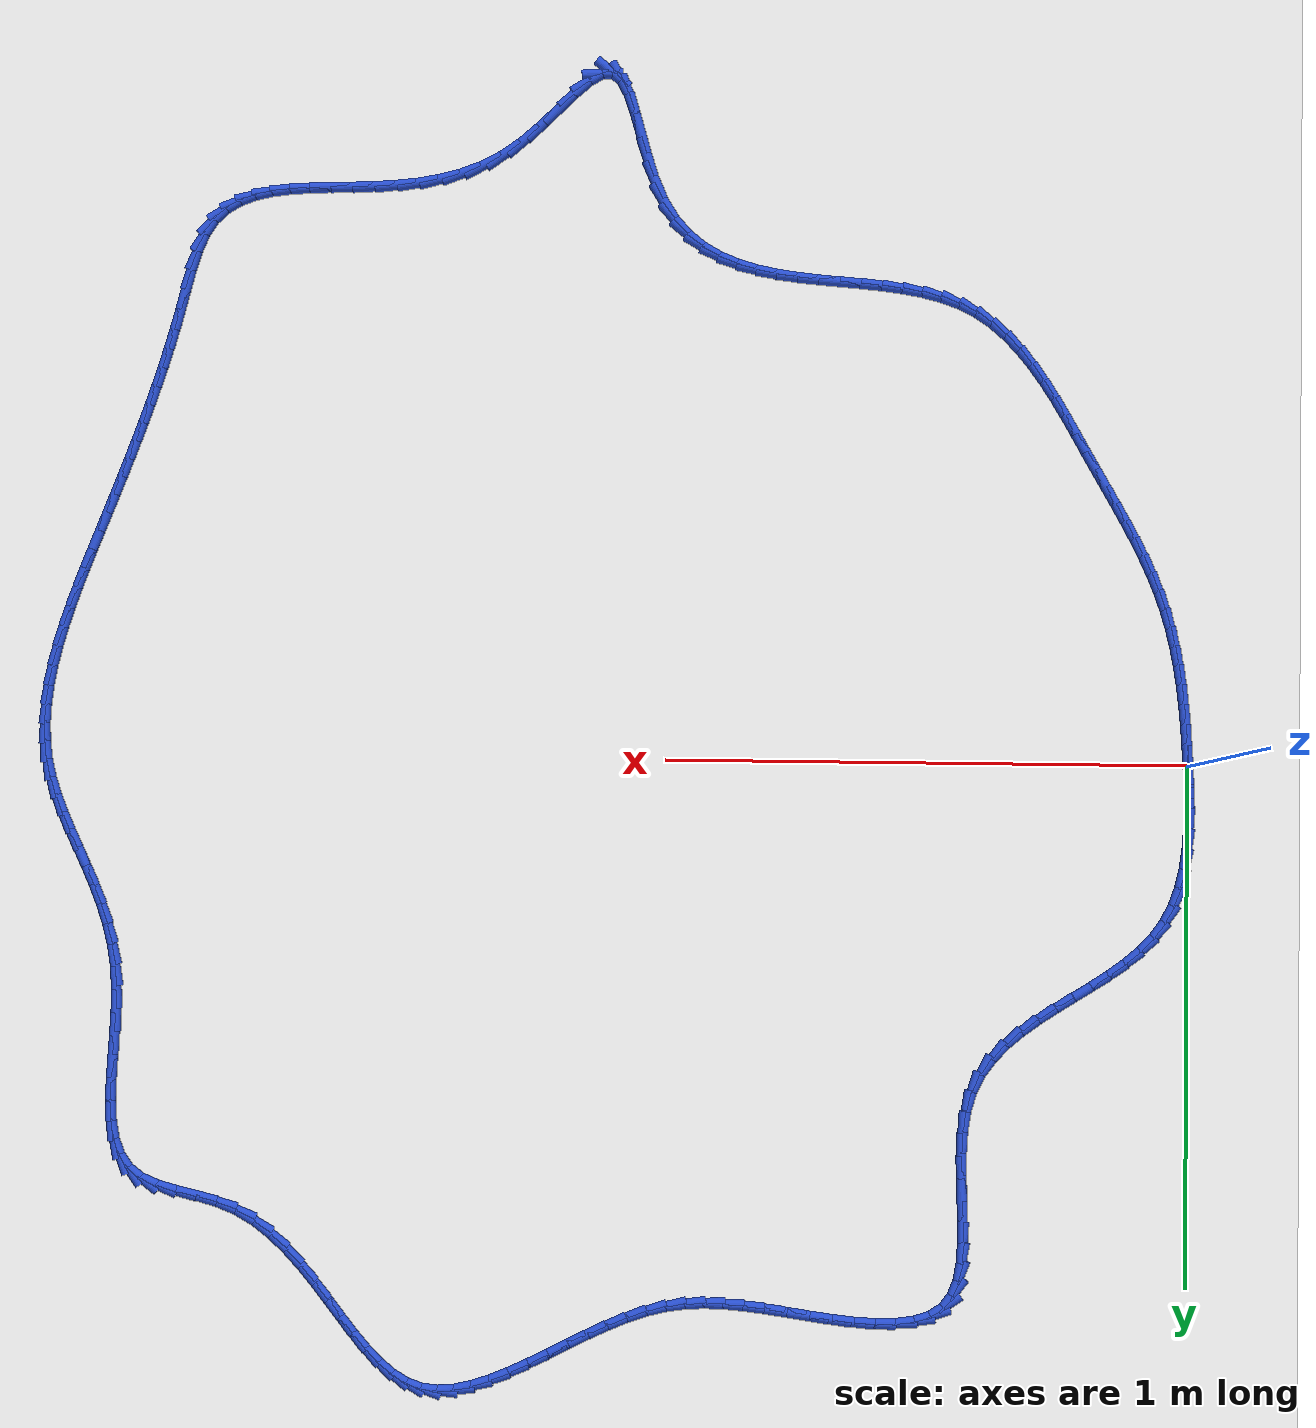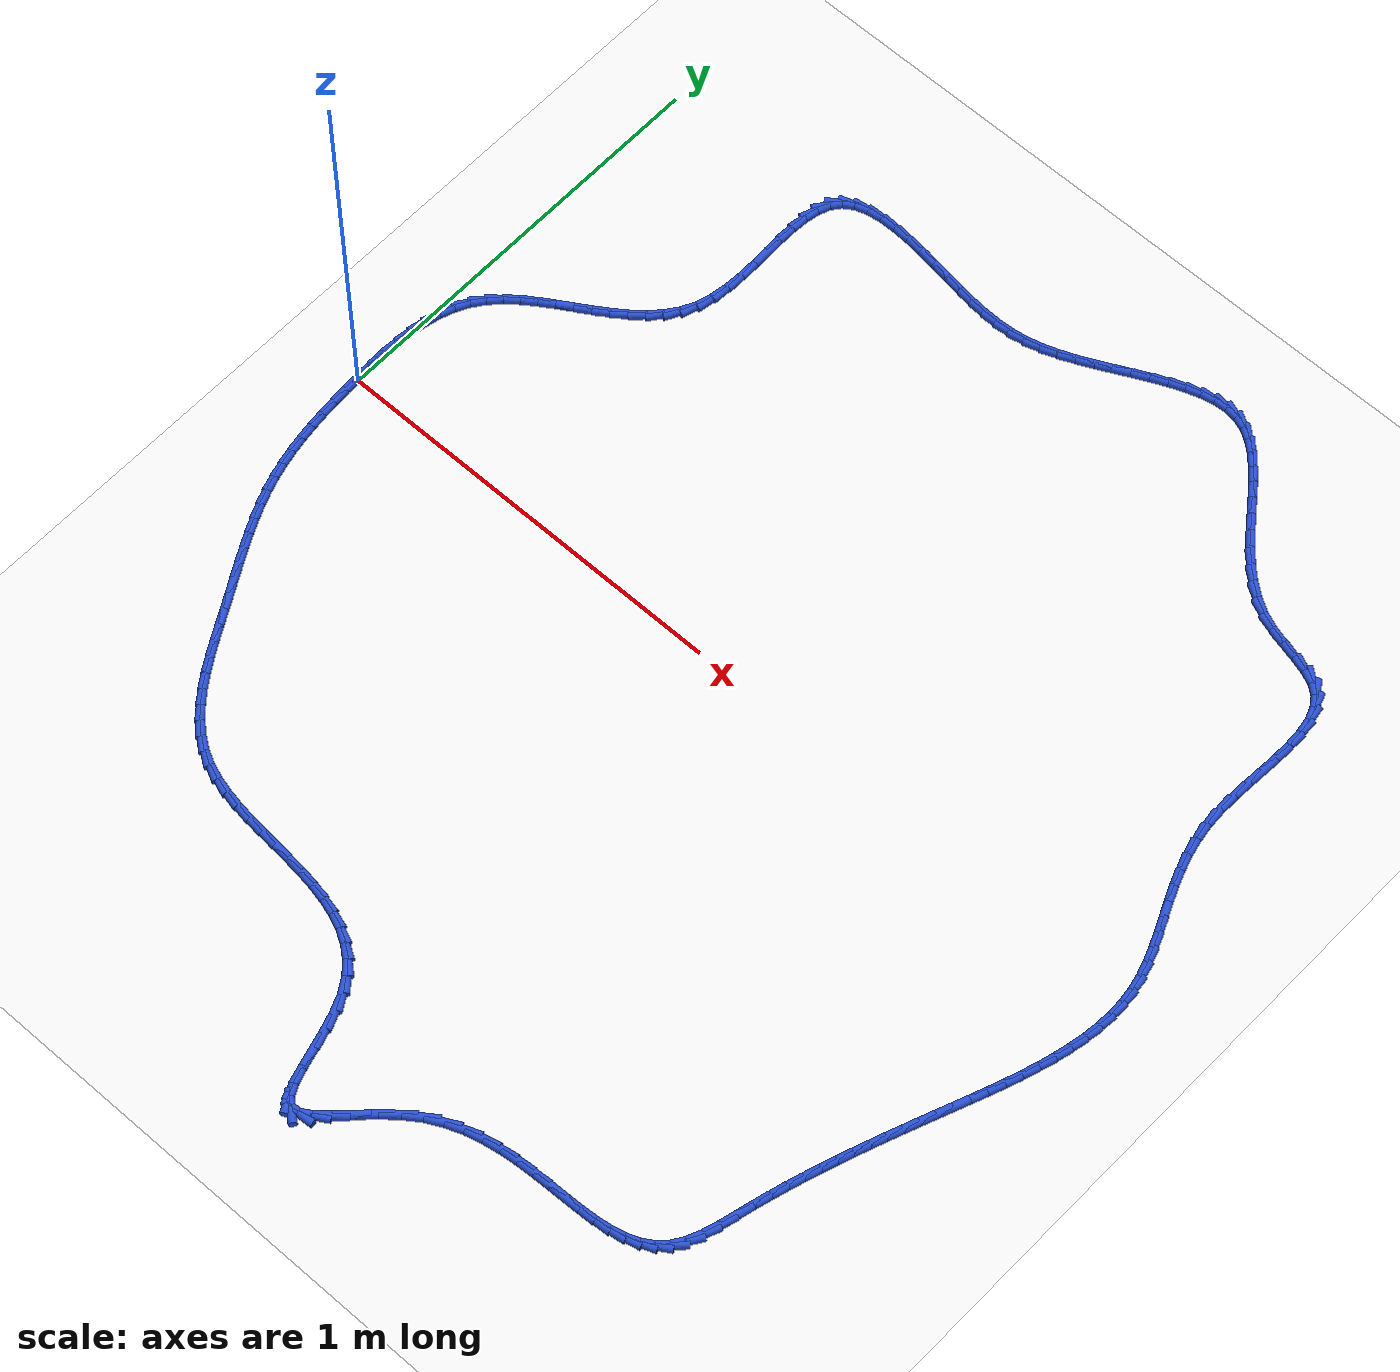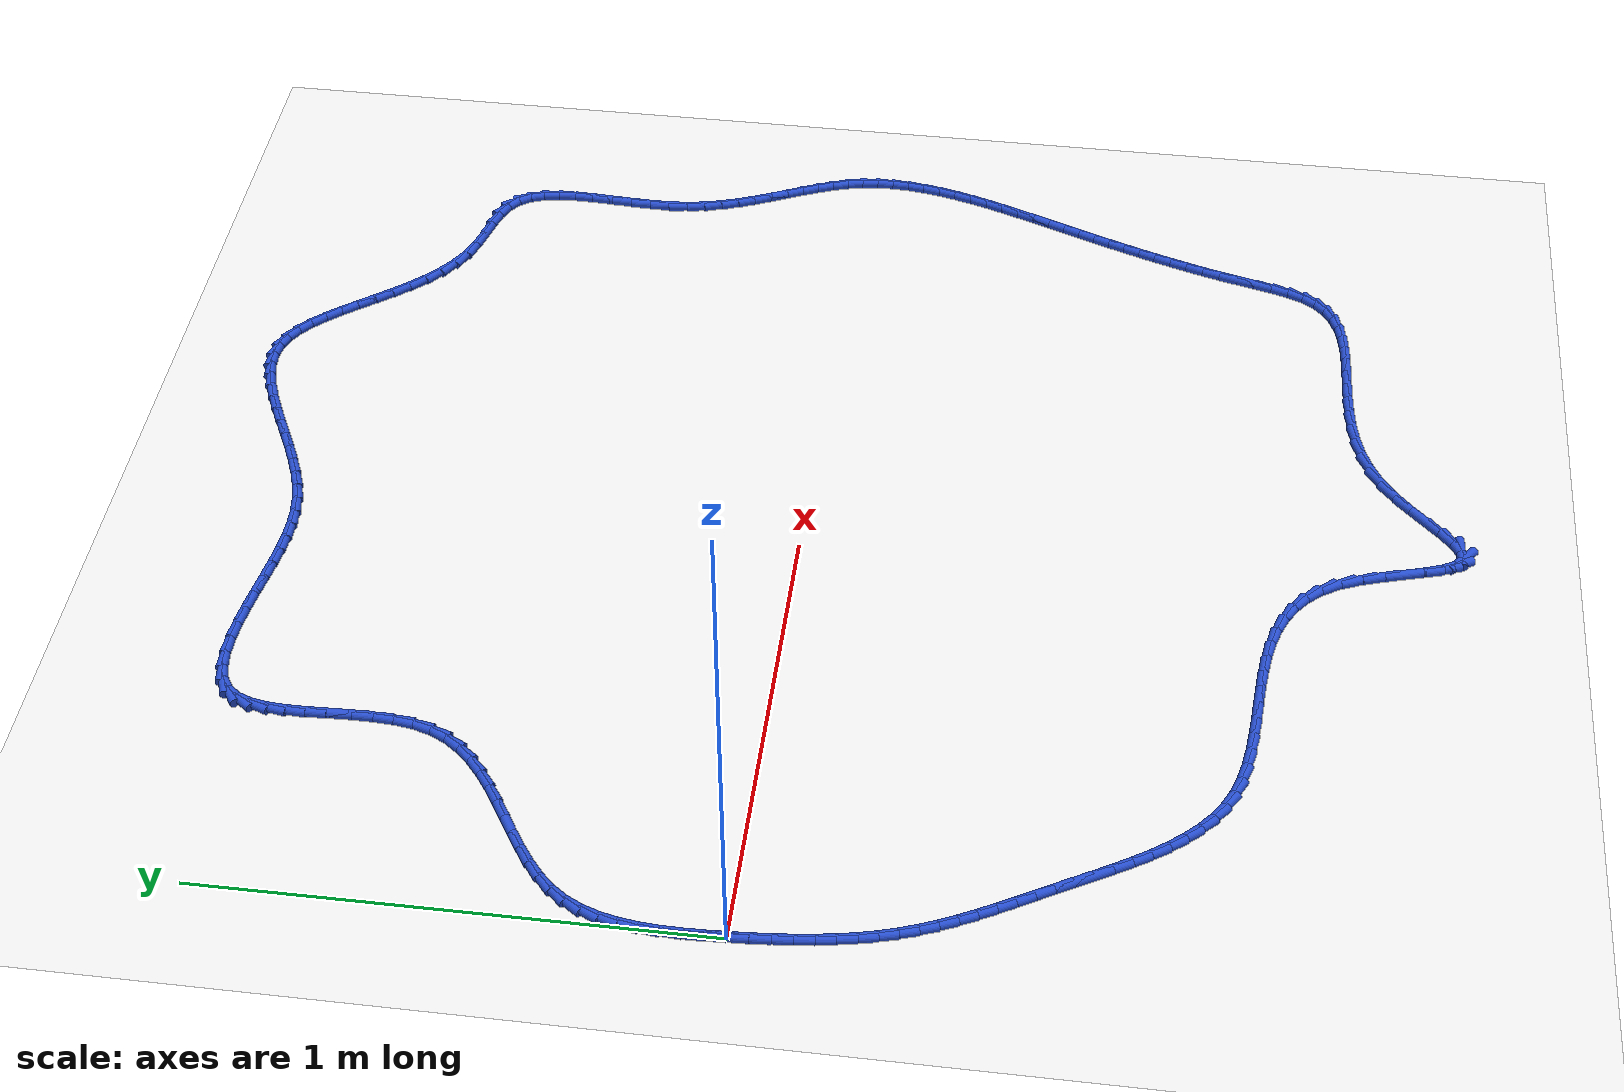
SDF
<sdf version="1.6">
 <world name="default">
  <light name="sun" type="directional">
   <pose>0 0 10 0 -0 0</pose>
   <diffuse>0.8 0.8 0.8 1</diffuse>
   <specular>0.2 0.2 0.2 1</specular>
   <attenuation>
    <range>1000</range>
    <constant>0.9</constant>
    <linear>0.01</linear>
    <quadratic>0.001</quadratic>
   </attenuation>
   <direction>-0.5 0.1 -0.9</direction>
  </light>
  <model name="ground_plane">
   <static>1</static>
   <link name="link">
    <collision name="collision">
     <geometry><plane><normal>0 0 1</normal><size>100 100</size></plane></geometry>
     <surface><friction><ode><mu>100</mu><mu2>50</mu2></ode></friction></surface>
    </collision>
    <visual name="visual">
     <cast_shadows>0</cast_shadows>
     <geometry><plane><normal>0 0 1</normal><size>100 100</size></plane></geometry>
     <material>
      <script><uri>file://media/materials/scripts/gazebo.material</uri><name>Gazebo/WhiteGlow</name></script>
     </material>
    </visual>
   </link>
  </model>
  <gravity>0 0 -9.8</gravity>
  <magnetic_field>6e-06 2.3e-05 -4.2e-05</magnetic_field>
  <atmosphere type="adiabatic"/>
  <physics name="default_physics" default="0" type="ode">
   <max_step_size>0.001</max_step_size>
   <real_time_factor>1</real_time_factor>
   <real_time_update_rate>1000</real_time_update_rate>
  </physics>
  <scene><ambient>0.4 0.4 0.4 1</ambient><background>0.7 0.7 0.7 1</background><shadows>1</shadows></scene>
  <spherical_coordinates>
   <surface_model>EARTH_WGS84</surface_model>
   <latitude_deg>0</latitude_deg>
   <longitude_deg>0</longitude_deg>
   <elevation>0</elevation>
   <heading_deg>0</heading_deg>
  </spherical_coordinates>
  <model name="line">
   <link name="link_0">
    <pose>-1.1058862159352145e-17 6.245004513516506e-17 0.01 0 1.57 -1.5275356418402912</pose>
    <collision name="collision">
     <geometry><cylinder><radius>0.01</radius><length>0.08</length></cylinder></geometry>
    </collision>
    <visual name="visual">
     <material>
      <script><name>Gazebo/Blue</name><uri>file://media/materials/scripts/gazebo.material</uri></script>
     </material>
     <geometry><cylinder><radius>0.01</radius><length>0.08</length></cylinder></geometry>
    </visual>
   </link>
   <link name="link_1">
    <pose>-0.001732869755976206 0.04003146525691955 0.01 0 1.57 -1.5516477831592397</pose>
    <collision name="collision">
     <geometry><cylinder><radius>0.01</radius><length>0.08</length></cylinder></geometry>
    </collision>
    <visual name="visual">
     <material>
      <script><name>Gazebo/Blue</name><uri>file://media/materials/scripts/gazebo.material</uri></script>
     </material>
     <geometry><cylinder><radius>0.01</radius><length>0.08</length></cylinder></geometry>
    </visual>
   </link>
   <link name="link_2">
    <pose>-0.0025025522690324815 0.08022190757347675 0.01 0 1.57 1.5524722743471855</pose>
    <collision name="collision">
     <geometry><cylinder><radius>0.01</radius><length>0.08</length></cylinder></geometry>
    </collision>
    <visual name="visual">
     <material>
      <script><name>Gazebo/Blue</name><uri>file://media/materials/scripts/gazebo.material</uri></script>
     </material>
     <geometry><cylinder><radius>0.01</radius><length>0.08</length></cylinder></geometry>
    </visual>
   </link>
   <link name="link_3">
    <pose>-0.001771156139702708 0.12013198036291048 0.01 0 1.57 1.500223726393946</pose>
    <collision name="collision">
     <geometry><cylinder><radius>0.01</radius><length>0.08</length></cylinder></geometry>
    </collision>
    <visual name="visual">
     <material>
      <script><name>Gazebo/Blue</name><uri>file://media/materials/scripts/gazebo.material</uri></script>
     </material>
     <geometry><cylinder><radius>0.01</radius><length>0.08</length></cylinder></geometry>
    </visual>
   </link>
   <link name="link_4">
    <pose>0.0009992100314792467 0.1593223370384596 0.01 0 1.57 1.43111125408944</pose>
    <collision name="collision">
     <geometry><cylinder><radius>0.01</radius><length>0.08</length></cylinder></geometry>
    </collision>
    <visual name="visual">
     <material>
      <script><name>Gazebo/Blue</name><uri>file://media/materials/scripts/gazebo.material</uri></script>
     </material>
     <geometry><cylinder><radius>0.01</radius><length>0.08</length></cylinder></geometry>
    </visual>
   </link>
   <link name="link_5">
    <pose>0.006346437643979517 0.19735363101336284 0.01 0 1.57 1.3425805001648072</pose>
    <collision name="collision">
     <geometry><cylinder><radius>0.01</radius><length>0.08</length></cylinder></geometry>
    </collision>
    <visual name="visual">
     <material>
      <script><name>Gazebo/Blue</name><uri>file://media/materials/scripts/gazebo.material</uri></script>
     </material>
     <geometry><cylinder><radius>0.01</radius><length>0.08</length></cylinder></geometry>
    </visual>
   </link>
   <link name="link_6">
    <pose>0.014808418097264221 0.23378651570085904 0.01 0 1.57 1.232145863026751</pose>
    <collision name="collision">
     <geometry><cylinder><radius>0.01</radius><length>0.08</length></cylinder></geometry>
    </collision>
    <visual name="visual">
     <material>
      <script><name>Gazebo/Blue</name><uri>file://media/materials/scripts/gazebo.material</uri></script>
     </material>
     <geometry><cylinder><radius>0.01</radius><length>0.08</length></cylinder></geometry>
    </visual>
   </link>
   <link name="link_7">
    <pose>0.026923042790799514 0.2681816445141871 0.01 0 1.57 1.098510501969893</pose>
    <collision name="collision">
     <geometry><cylinder><radius>0.01</radius><length>0.08</length></cylinder></geometry>
    </collision>
    <visual name="visual">
     <material>
      <script><name>Gazebo/Blue</name><uri>file://media/materials/scripts/gazebo.material</uri></script>
     </material>
     <geometry><cylinder><radius>0.01</radius><length>0.08</length></cylinder></geometry>
    </visual>
   </link>
   <link name="link_8">
    <pose>0.0432282031240515 0.30009967086658573 0.01 0 1.57 0.9460700117547107</pose>
    <collision name="collision">
     <geometry><cylinder><radius>0.01</radius><length>0.08</length></cylinder></geometry>
    </collision>
    <visual name="visual">
     <material>
      <script><name>Gazebo/Blue</name><uri>file://media/materials/scripts/gazebo.material</uri></script>
     </material>
     <geometry><cylinder><radius>0.01</radius><length>0.08</length></cylinder></geometry>
    </visual>
   </link>
   <link name="link_9">
    <pose>0.06418155043998908 0.3291584232177059 0.01 0 1.57 0.8078296274266489</pose>
    <collision name="collision">
     <geometry><cylinder><radius>0.01</radius><length>0.08</length></cylinder></geometry>
    </collision>
    <visual name="visual">
     <material>
      <script><name>Gazebo/Blue</name><uri>file://media/materials/scripts/gazebo.material</uri></script>
     </material>
     <geometry><cylinder><radius>0.01</radius><length>0.08</length></cylinder></geometry>
    </visual>
   </link>
   <link name="link_10">
    <pose>0.08942296959469796 0.3555584294778584 0.01 0 1.57 0.7023490302393617</pose>
    <collision name="collision">
     <geometry><cylinder><radius>0.01</radius><length>0.08</length></cylinder></geometry>
    </collision>
    <visual name="visual">
     <material>
      <script><name>Gazebo/Blue</name><uri>file://media/materials/scripts/gazebo.material</uri></script>
     </material>
     <geometry><cylinder><radius>0.01</radius><length>0.08</length></cylinder></geometry>
    </visual>
   </link>
   <link name="link_11">
    <pose>0.11811468813111066 0.3798405722410467 0.01 0 1.57 0.627689161497716</pose>
    <collision name="collision">
     <geometry><cylinder><radius>0.01</radius><length>0.08</length></cylinder></geometry>
    </collision>
    <visual name="visual">
     <material>
      <script><name>Gazebo/Blue</name><uri>file://media/materials/scripts/gazebo.material</uri></script>
     </material>
     <geometry><cylinder><radius>0.01</radius><length>0.08</length></cylinder></geometry>
    </visual>
   </link>
   <link name="link_12">
    <pose>0.14941294272033548 0.40255000289655707 0.01 0 1.57 0.5804512296174468</pose>
    <collision name="collision">
     <geometry><cylinder><radius>0.01</radius><length>0.08</length></cylinder></geometry>
    </collision>
    <visual name="visual">
     <material>
      <script><name>Gazebo/Blue</name><uri>file://media/materials/scripts/gazebo.material</uri></script>
     </material>
     <geometry><cylinder><radius>0.01</radius><length>0.08</length></cylinder></geometry>
    </visual>
   </link>
   <link name="link_13">
    <pose>0.1824739700334807 0.4242318728336751 0.01 0 1.57 0.5577934172182518</pose>
    <collision name="collision">
     <geometry><cylinder><radius>0.01</radius><length>0.08</length></cylinder></geometry>
    </collision>
    <visual name="visual">
     <material>
      <script><name>Gazebo/Blue</name><uri>file://media/materials/scripts/gazebo.material</uri></script>
     </material>
     <geometry><cylinder><radius>0.01</radius><length>0.08</length></cylinder></geometry>
    </visual>
   </link>
   <link name="link_14">
    <pose>0.21645400674165438 0.4454313334416864 0.01 0 1.57 0.5581272599864323</pose>
    <collision name="collision">
     <geometry><cylinder><radius>0.01</radius><length>0.08</length></cylinder></geometry>
    </collision>
    <visual name="visual">
     <material>
      <script><name>Gazebo/Blue</name><uri>file://media/materials/scripts/gazebo.material</uri></script>
     </material>
     <geometry><cylinder><radius>0.01</radius><length>0.08</length></cylinder></geometry>
    </visual>
   </link>
   <link name="link_15">
    <pose>0.25050928951596463 0.46669353610987685 0.01 0 1.57 0.5812949089435681</pose>
    <collision name="collision">
     <geometry><cylinder><radius>0.01</radius><length>0.08</length></cylinder></geometry>
    </collision>
    <visual name="visual">
     <material>
      <script><name>Gazebo/Blue</name><uri>file://media/materials/scripts/gazebo.material</uri></script>
     </material>
     <geometry><cylinder><radius>0.01</radius><length>0.08</length></cylinder></geometry>
    </visual>
   </link>
   <link name="link_16">
    <pose>0.28379605502752003 0.48856363222753263 0.01 0 1.57 0.6285309322067728</pose>
    <collision name="collision">
     <geometry><cylinder><radius>0.01</radius><length>0.08</length></cylinder></geometry>
    </collision>
    <visual name="visual">
     <material>
      <script><name>Gazebo/Blue</name><uri>file://media/materials/scripts/gazebo.material</uri></script>
     </material>
     <geometry><cylinder><radius>0.01</radius><length>0.08</length></cylinder></geometry>
    </visual>
   </link>
   <link name="link_17">
    <pose>0.31547053994742863 0.511586773183939 0.01 0 1.57 0.7022178572623757</pose>
    <collision name="collision">
     <geometry><cylinder><radius>0.01</radius><length>0.08</length></cylinder></geometry>
    </collision>
    <visual name="visual">
     <material>
      <script><name>Gazebo/Blue</name><uri>file://media/materials/scripts/gazebo.material</uri></script>
     </material>
     <geometry><cylinder><radius>0.01</radius><length>0.08</length></cylinder></geometry>
    </visual>
   </link>
   <link name="link_18">
    <pose>0.34468898094679856 0.5363081103683821 0.01 0 1.57 0.8051759437182795</pose>
    <collision name="collision">
     <geometry><cylinder><radius>0.01</radius><length>0.08</length></cylinder></geometry>
    </collision>
    <visual name="visual">
     <material>
      <script><name>Gazebo/Blue</name><uri>file://media/materials/scripts/gazebo.material</uri></script>
     </material>
     <geometry><cylinder><radius>0.01</radius><length>0.08</length></cylinder></geometry>
    </visual>
   </link>
   <link name="link_19">
    <pose>0.3706076146967381 0.5632727951701477 0.01 0 1.57 0.9390084885521963</pose>
    <collision name="collision">
     <geometry><cylinder><radius>0.01</radius><length>0.08</length></cylinder></geometry>
    </collision>
    <visual name="visual">
     <material>
      <script><name>Gazebo/Blue</name><uri>file://media/materials/scripts/gazebo.material</uri></script>
     </material>
     <geometry><cylinder><radius>0.01</radius><length>0.08</length></cylinder></geometry>
    </visual>
   </link>
   <link name="link_20">
    <pose>0.39238267786835557 0.5930259789785216 0.01 0 1.57 1.1012590065751653</pose>
    <collision name="collision">
     <geometry><cylinder><radius>0.01</radius><length>0.08</length></cylinder></geometry>
    </collision>
    <visual name="visual">
     <material>
      <script><name>Gazebo/Blue</name><uri>file://media/materials/scripts/gazebo.material</uri></script>
     </material>
     <geometry><cylinder><radius>0.01</radius><length>0.08</length></cylinder></geometry>
    </visual>
   </link>
   <link name="link_21">
    <pose>0.409170407132759 0.6261128131827894 0.01 0 1.57 1.2771496763540042</pose>
    <collision name="collision">
     <geometry><cylinder><radius>0.01</radius><length>0.08</length></cylinder></geometry>
    </collision>
    <visual name="visual">
     <material>
      <script><name>Gazebo/Blue</name><uri>file://media/materials/scripts/gazebo.material</uri></script>
     </material>
     <geometry><cylinder><radius>0.01</radius><length>0.08</length></cylinder></geometry>
    </visual>
   </link>
   <link name="link_22">
    <pose>0.42030753806117166 0.6629433485379617 0.01 0 1.57 1.418424269235094</pose>
    <collision name="collision">
     <geometry><cylinder><radius>0.01</radius><length>0.08</length></cylinder></geometry>
    </collision>
    <visual name="visual">
     <material>
      <script><name>Gazebo/Blue</name><uri>file://media/materials/scripts/gazebo.material</uri></script>
     </material>
     <geometry><cylinder><radius>0.01</radius><length>0.08</length></cylinder></geometry>
    </visual>
   </link>
   <link name="link_23">
    <pose>0.4264495999379652 0.7029405391075337 0.01 0 1.57 1.5142072374921347</pose>
    <collision name="collision">
     <geometry><cylinder><radius>0.01</radius><length>0.08</length></cylinder></geometry>
    </collision>
    <visual name="visual">
     <material>
      <script><name>Gazebo/Blue</name><uri>file://media/materials/scripts/gazebo.material</uri></script>
     </material>
     <geometry><cylinder><radius>0.01</radius><length>0.08</length></cylinder></geometry>
    </visual>
   </link>
   <link name="link_24">
    <pose>0.4288373111412763 0.7450893339716551 0.01 0 1.57 -1.567948016073289</pose>
    <collision name="collision">
     <geometry><cylinder><radius>0.01</radius><length>0.08</length></cylinder></geometry>
    </collision>
    <visual name="visual">
     <material>
      <script><name>Gazebo/Blue</name><uri>file://media/materials/scripts/gazebo.material</uri></script>
     </material>
     <geometry><cylinder><radius>0.01</radius><length>0.08</length></cylinder></geometry>
    </visual>
   </link>
   <link name="link_25">
    <pose>0.42871402630668165 0.7883727090125657 0.01 0 1.57 -1.5387589881703392</pose>
    <collision name="collision">
     <geometry><cylinder><radius>0.01</radius><length>0.08</length></cylinder></geometry>
    </collision>
    <visual name="visual">
     <material>
      <script><name>Gazebo/Blue</name><uri>file://media/materials/scripts/gazebo.material</uri></script>
     </material>
     <geometry><cylinder><radius>0.01</radius><length>0.08</length></cylinder></geometry>
    </visual>
   </link>
   <link name="link_26">
    <pose>0.4273231000697584 0.831773640112506 0.01 0 1.57 -1.5375106418253857</pose>
    <collision name="collision">
     <geometry><cylinder><radius>0.01</radius><length>0.08</length></cylinder></geometry>
    </collision>
    <visual name="visual">
     <material>
      <script><name>Gazebo/Blue</name><uri>file://media/materials/scripts/gazebo.material</uri></script>
     </material>
     <geometry><cylinder><radius>0.01</radius><length>0.08</length></cylinder></geometry>
    </visual>
   </link>
   <link name="link_27">
    <pose>0.4259078870660832 0.8742751031537159 0.01 0 1.57 -1.5659634144249912</pose>
    <collision name="collision">
     <geometry><cylinder><radius>0.01</radius><length>0.08</length></cylinder></geometry>
    </collision>
    <visual name="visual">
     <material>
      <script><name>Gazebo/Blue</name><uri>file://media/materials/scripts/gazebo.material</uri></script>
     </material>
     <geometry><cylinder><radius>0.01</radius><length>0.08</length></cylinder></geometry>
    </visual>
   </link>
   <link name="link_28">
    <pose>0.42571174193123307 0.9148600740184358 0.01 0 1.57 1.5106778942452932</pose>
    <collision name="collision">
     <geometry><cylinder><radius>0.01</radius><length>0.08</length></cylinder></geometry>
    </collision>
    <visual name="visual">
     <material>
      <script><name>Gazebo/Blue</name><uri>file://media/materials/scripts/gazebo.material</uri></script>
     </material>
     <geometry><cylinder><radius>0.01</radius><length>0.08</length></cylinder></geometry>
    </visual>
   </link>
   <link name="link_29">
    <pose>0.42797801930078483 0.9525115285889053 0.01 0 1.57 1.3954095687814998</pose>
    <collision name="collision">
     <geometry><cylinder><radius>0.01</radius><length>0.08</length></cylinder></geometry>
    </collision>
    <visual name="visual">
     <material>
      <script><name>Gazebo/Blue</name><uri>file://media/materials/scripts/gazebo.material</uri></script>
     </material>
     <geometry><cylinder><radius>0.01</radius><length>0.08</length></cylinder></geometry>
    </visual>
   </link>
   <link name="link_30">
    <pose>0.43395007381031536 0.9862124427473652 0.01 0 1.57 1.2075728823514587</pose>
    <collision name="collision">
     <geometry><cylinder><radius>0.01</radius><length>0.08</length></cylinder></geometry>
    </collision>
    <visual name="visual">
     <material>
      <script><name>Gazebo/Blue</name><uri>file://media/materials/scripts/gazebo.material</uri></script>
     </material>
     <geometry><cylinder><radius>0.01</radius><length>0.08</length></cylinder></geometry>
    </visual>
   </link>
   <link name="link_31">
    <pose>0.4448712600954017 1.0149457923760554 0.01 0 1.57 0.9258310234081023</pose>
    <collision name="collision">
     <geometry><cylinder><radius>0.01</radius><length>0.08</length></cylinder></geometry>
    </collision>
    <visual name="visual">
     <material>
      <script><name>Gazebo/Blue</name><uri>file://media/materials/scripts/gazebo.material</uri></script>
     </material>
     <geometry><cylinder><radius>0.01</radius><length>0.08</length></cylinder></geometry>
    </visual>
   </link>
   <link name="link_32">
    <pose>0.46198493279162045 1.0376945533572157 0.01 0 1.57 0.586469996426578</pose>
    <collision name="collision">
     <geometry><cylinder><radius>0.01</radius><length>0.08</length></cylinder></geometry>
    </collision>
    <visual name="visual">
     <material>
      <script><name>Gazebo/Blue</name><uri>file://media/materials/scripts/gazebo.material</uri></script>
     </material>
     <geometry><cylinder><radius>0.01</radius><length>0.08</length></cylinder></geometry>
    </visual>
   </link>
   <link name="link_33">
    <pose>0.48614955441017244 1.0537508608491075 0.01 0 1.57 0.31651467061197514</pose>
    <collision name="collision">
     <geometry><cylinder><radius>0.01</radius><length>0.08</length></cylinder></geometry>
    </collision>
    <visual name="visual">
     <material>
      <script><name>Gazebo/Blue</name><uri>file://media/materials/scripts/gazebo.material</uri></script>
     </material>
     <geometry><cylinder><radius>0.01</radius><length>0.08</length></cylinder></geometry>
    </visual>
   </link>
   <link name="link_34">
    <pose>0.5165883333295642 1.0637203452772463 0.01 0 1.57 0.1354139370446253</pose>
    <collision name="collision">
     <geometry><cylinder><radius>0.01</radius><length>0.08</length></cylinder></geometry>
    </collision>
    <visual name="visual">
     <material>
      <script><name>Gazebo/Blue</name><uri>file://media/materials/scripts/gazebo.material</uri></script>
     </material>
     <geometry><cylinder><radius>0.01</radius><length>0.08</length></cylinder></geometry>
    </visual>
   </link>
   <link name="link_35">
    <pose>0.5520902747579276 1.0685574047589195 0.01 0 1.57 0.016744726085475014</pose>
    <collision name="collision">
     <geometry><cylinder><radius>0.01</radius><length>0.08</length></cylinder></geometry>
    </collision>
    <visual name="visual">
     <material>
      <script><name>Gazebo/Blue</name><uri>file://media/materials/scripts/gazebo.material</uri></script>
     </material>
     <geometry><cylinder><radius>0.01</radius><length>0.08</length></cylinder></geometry>
    </visual>
   </link>
   <link name="link_36">
    <pose>0.5914443805845806 1.0692164400772033 0.01 0 1.57 -0.06099274885537861</pose>
    <collision name="collision">
     <geometry><cylinder><radius>0.01</radius><length>0.08</length></cylinder></geometry>
    </collision>
    <visual name="visual">
     <material>
      <script><name>Gazebo/Blue</name><uri>file://media/materials/scripts/gazebo.material</uri></script>
     </material>
     <geometry><cylinder><radius>0.01</radius><length>0.08</length></cylinder></geometry>
    </visual>
   </link>
   <link name="link_37">
    <pose>0.6334396526988426 1.066651852015175 0.01 0 1.57 -0.11085652130134405</pose>
    <collision name="collision">
     <geometry><cylinder><radius>0.01</radius><length>0.08</length></cylinder></geometry>
    </collision>
    <visual name="visual">
     <material>
      <script><name>Gazebo/Blue</name><uri>file://media/materials/scripts/gazebo.material</uri></script>
     </material>
     <geometry><cylinder><radius>0.01</radius><length>0.08</length></cylinder></geometry>
    </visual>
   </link>
   <link name="link_38">
    <pose>0.6768650929900315 1.0618180413559113 0.01 0 1.57 -0.13995846597477396</pose>
    <collision name="collision">
     <geometry><cylinder><radius>0.01</radius><length>0.08</length></cylinder></geometry>
    </collision>
    <visual name="visual">
     <material>
      <script><name>Gazebo/Blue</name><uri>file://media/materials/scripts/gazebo.material</uri></script>
     </material>
     <geometry><cylinder><radius>0.01</radius><length>0.08</length></cylinder></geometry>
    </visual>
   </link>
   <link name="link_39">
    <pose>0.7205097033474658 1.0556694088824887 0.01 0 1.57 -0.15143723430762923</pose>
    <collision name="collision">
     <geometry><cylinder><radius>0.01</radius><length>0.08</length></cylinder></geometry>
    </collision>
    <visual name="visual">
     <material>
      <script><name>Gazebo/Blue</name><uri>file://media/materials/scripts/gazebo.material</uri></script>
     </material>
     <geometry><cylinder><radius>0.01</radius><length>0.08</length></cylinder></geometry>
    </visual>
   </link>
   <link name="link_40">
    <pose>0.763162485781373 1.049160355347872 0.01 0 1.57 -0.14589711013485016</pose>
    <collision name="collision">
     <geometry><cylinder><radius>0.01</radius><length>0.08</length></cylinder></geometry>
    </collision>
    <visual name="visual">
     <material>
      <script><name>Gazebo/Blue</name><uri>file://media/materials/scripts/gazebo.material</uri></script>
     </material>
     <geometry><cylinder><radius>0.01</radius><length>0.08</length></cylinder></geometry>
    </visual>
   </link>
   <link name="link_41">
    <pose>0.803893425054528 1.0431753027537694 0.01 0 1.57 -0.12379978470564273</pose>
    <collision name="collision">
     <geometry><cylinder><radius>0.01</radius><length>0.08</length></cylinder></geometry>
    </collision>
    <visual name="visual">
     <material>
      <script><name>Gazebo/Blue</name><uri>file://media/materials/scripts/gazebo.material</uri></script>
     </material>
     <geometry><cylinder><radius>0.01</radius><length>0.08</length></cylinder></geometry>
    </visual>
   </link>
   <link name="link_42">
    <pose>0.8428710797199511 1.0383250733121934 0.01 0 1.57 -0.0840111638354742</pose>
    <collision name="collision">
     <geometry><cylinder><radius>0.01</radius><length>0.08</length></cylinder></geometry>
    </collision>
    <visual name="visual">
     <material>
      <script><name>Gazebo/Blue</name><uri>file://media/materials/scripts/gazebo.material</uri></script>
     </material>
     <geometry><cylinder><radius>0.01</radius><length>0.08</length></cylinder></geometry>
    </visual>
   </link>
   <link name="link_43">
    <pose>0.8805324548568401 1.0351536326309319 0.01 0 1.57 -0.02578634755228146</pose>
    <collision name="collision">
     <geometry><cylinder><radius>0.01</radius><length>0.08</length></cylinder></geometry>
    </collision>
    <visual name="visual">
     <material>
      <script><name>Gazebo/Blue</name><uri>file://media/materials/scripts/gazebo.material</uri></script>
     </material>
     <geometry><cylinder><radius>0.01</radius><length>0.08</length></cylinder></geometry>
    </visual>
   </link>
   <link name="link_44">
    <pose>0.9173145555443931 1.0342049463177723 0.01 0 1.57 0.04998700060507502</pose>
    <collision name="collision">
     <geometry><cylinder><radius>0.01</radius><length>0.08</length></cylinder></geometry>
    </collision>
    <visual name="visual">
     <material>
      <script><name>Gazebo/Blue</name><uri>file://media/materials/scripts/gazebo.material</uri></script>
     </material>
     <geometry><cylinder><radius>0.01</radius><length>0.08</length></cylinder></geometry>
    </visual>
   </link>
   <link name="link_45">
    <pose>0.9536543868618078 1.0360229799805032 0.01 0 1.57 0.14022622272405869</pose>
    <collision name="collision">
     <geometry><cylinder><radius>0.01</radius><length>0.08</length></cylinder></geometry>
    </collision>
    <visual name="visual">
     <material>
      <script><name>Gazebo/Blue</name><uri>file://media/materials/scripts/gazebo.material</uri></script>
     </material>
     <geometry><cylinder><radius>0.01</radius><length>0.08</length></cylinder></geometry>
    </visual>
   </link>
   <link name="link_46">
    <pose>0.9899889538882825 1.041151699226912 0.01 0 1.57 0.23918329345192557</pose>
    <collision name="collision">
     <geometry><cylinder><radius>0.01</radius><length>0.08</length></cylinder></geometry>
    </collision>
    <visual name="visual">
     <material>
      <script><name>Gazebo/Blue</name><uri>file://media/materials/scripts/gazebo.material</uri></script>
     </material>
     <geometry><cylinder><radius>0.01</radius><length>0.08</length></cylinder></geometry>
    </visual>
   </link>
   <link name="link_47">
    <pose>1.0267462085621666 1.0501150020726417 0.01 0 1.57 0.3278573880570288</pose>
    <collision name="collision">
     <geometry><cylinder><radius>0.01</radius><length>0.08</length></cylinder></geometry>
    </collision>
    <visual name="visual">
     <material>
      <script><name>Gazebo/Blue</name><uri>file://media/materials/scripts/gazebo.material</uri></script>
     </material>
     <geometry><cylinder><radius>0.01</radius><length>0.08</length></cylinder></geometry>
    </visual>
   </link>
   <link name="link_48">
    <pose>1.0640716038957485 1.0628105869276183 0.01 0 1.57 0.39207253317812685</pose>
    <collision name="collision">
     <geometry><cylinder><radius>0.01</radius><length>0.08</length></cylinder></geometry>
    </collision>
    <visual name="visual">
     <material>
      <script><name>Gazebo/Blue</name><uri>file://media/materials/scripts/gazebo.material</uri></script>
     </material>
     <geometry><cylinder><radius>0.01</radius><length>0.08</length></cylinder></geometry>
    </visual>
   </link>
   <link name="link_49">
    <pose>1.1017793888955296 1.0784019907636098 0.01 0 1.57 0.4350872213222646</pose>
    <collision name="collision">
     <geometry><cylinder><radius>0.01</radius><length>0.08</length></cylinder></geometry>
    </collision>
    <visual name="visual">
     <material>
      <script><name>Gazebo/Blue</name><uri>file://media/materials/scripts/gazebo.material</uri></script>
     </material>
     <geometry><cylinder><radius>0.01</radius><length>0.08</length></cylinder></geometry>
    </visual>
   </link>
   <link name="link_50">
    <pose>1.1396649410901403 1.0960109192004315 0.01 0 1.57 0.4598115246713203</pose>
    <collision name="collision">
     <geometry><cylinder><radius>0.01</radius><length>0.08</length></cylinder></geometry>
    </collision>
    <visual name="visual">
     <material>
      <script><name>Gazebo/Blue</name><uri>file://media/materials/scripts/gazebo.material</uri></script>
     </material>
     <geometry><cylinder><radius>0.01</radius><length>0.08</length></cylinder></geometry>
    </visual>
   </link>
   <link name="link_51">
    <pose>1.1775236380082104 1.1147590778578984 0.01 0 1.57 0.46779521064507407</pose>
    <collision name="collision">
     <geometry><cylinder><radius>0.01</radius><length>0.08</length></cylinder></geometry>
    </collision>
    <visual name="visual">
     <material>
      <script><name>Gazebo/Blue</name><uri>file://media/materials/scripts/gazebo.material</uri></script>
     </material>
     <geometry><cylinder><radius>0.01</radius><length>0.08</length></cylinder></geometry>
    </visual>
   </link>
   <link name="link_52">
    <pose>1.2151508571783698 1.1337681723558262 0.01 0 1.57 0.4592536567526458</pose>
    <collision name="collision">
     <geometry><cylinder><radius>0.01</radius><length>0.08</length></cylinder></geometry>
    </collision>
    <visual name="visual">
     <material>
      <script><name>Gazebo/Blue</name><uri>file://media/materials/scripts/gazebo.material</uri></script>
     </material>
     <geometry><cylinder><radius>0.01</radius><length>0.08</length></cylinder></geometry>
    </visual>
   </link>
   <link name="link_53">
    <pose>1.252341976129249 1.15215990831403 0.01 0 1.57 0.4330091335270411</pose>
    <collision name="collision">
     <geometry><cylinder><radius>0.01</radius><length>0.08</length></cylinder></geometry>
    </collision>
    <visual name="visual">
     <material>
      <script><name>Gazebo/Blue</name><uri>file://media/materials/scripts/gazebo.material</uri></script>
     </material>
     <geometry><cylinder><radius>0.01</radius><length>0.08</length></cylinder></geometry>
    </visual>
   </link>
   <link name="link_54">
    <pose>1.2888923723894778 1.169055991352325 0.01 0 1.57 0.3862902853971466</pose>
    <collision name="collision">
     <geometry><cylinder><radius>0.01</radius><length>0.08</length></cylinder></geometry>
    </collision>
    <visual name="visual">
     <material>
      <script><name>Gazebo/Blue</name><uri>file://media/materials/scripts/gazebo.material</uri></script>
     </material>
     <geometry><cylinder><radius>0.01</radius><length>0.08</length></cylinder></geometry>
    </visual>
   </link>
   <link name="link_55">
    <pose>1.3245974234876863 1.1835781270905268 0.01 0 1.57 0.31441437125018074</pose>
    <collision name="collision">
     <geometry><cylinder><radius>0.01</radius><length>0.08</length></cylinder></geometry>
    </collision>
    <visual name="visual">
     <material>
      <script><name>Gazebo/Blue</name><uri>file://media/materials/scripts/gazebo.material</uri></script>
     </material>
     <geometry><cylinder><radius>0.01</radius><length>0.08</length></cylinder></geometry>
    </visual>
   </link>
   <link name="link_56">
    <pose>1.359252506952505 1.1948480211484505 0.01 0 1.57 0.2105811546970328</pose>
    <collision name="collision">
     <geometry><cylinder><radius>0.01</radius><length>0.08</length></cylinder></geometry>
    </collision>
    <visual name="visual">
     <material>
      <script><name>Gazebo/Blue</name><uri>file://media/materials/scripts/gazebo.material</uri></script>
     </material>
     <geometry><cylinder><radius>0.01</radius><length>0.08</length></cylinder></geometry>
    </visual>
   </link>
   <link name="link_57">
    <pose>1.3926530003125634 1.2019873791459112 0.01 0 1.57 0.06660272497537507</pose>
    <collision name="collision">
     <geometry><cylinder><radius>0.01</radius><length>0.08</length></cylinder></geometry>
    </collision>
    <visual name="visual">
     <material>
      <script><name>Gazebo/Blue</name><uri>file://media/materials/scripts/gazebo.material</uri></script>
     </material>
     <geometry><cylinder><radius>0.01</radius><length>0.08</length></cylinder></geometry>
    </visual>
   </link>
   <link name="link_58">
    <pose>1.424594281096492 1.2041179067027252 0.01 0 1.57 -0.12344162327158452</pose>
    <collision name="collision">
     <geometry><cylinder><radius>0.01</radius><length>0.08</length></cylinder></geometry>
    </collision>
    <visual name="visual">
     <material>
      <script><name>Gazebo/Blue</name><uri>file://media/materials/scripts/gazebo.material</uri></script>
     </material>
     <geometry><cylinder><radius>0.01</radius><length>0.08</length></cylinder></geometry>
    </visual>
   </link>
   <link name="link_59">
    <pose>1.454871726832921 1.2003613094387067 0.01 0 1.57 -0.34734658807763835</pose>
    <collision name="collision">
     <geometry><cylinder><radius>0.01</radius><length>0.08</length></cylinder></geometry>
    </collision>
    <visual name="visual">
     <material>
      <script><name>Gazebo/Blue</name><uri>file://media/materials/scripts/gazebo.material</uri></script>
     </material>
     <geometry><cylinder><radius>0.01</radius><length>0.08</length></cylinder></geometry>
    </visual>
   </link>
   <link name="link_60">
    <pose>1.4833486312748978 1.1900519743539284 0.01 0 1.57 -0.5453853863044464</pose>
    <collision name="collision">
     <geometry><cylinder><radius>0.01</radius><length>0.08</length></cylinder></geometry>
    </collision>
    <visual name="visual">
     <material>
      <script><name>Gazebo/Blue</name><uri>file://media/materials/scripts/gazebo.material</uri></script>
     </material>
     <geometry><cylinder><radius>0.01</radius><length>0.08</length></cylinder></geometry>
    </visual>
   </link>
   <link name="link_61">
    <pose>1.5102692411695982 1.1737172524169184 0.01 0 1.57 -0.6939582385366846</pose>
    <collision name="collision">
     <geometry><cylinder><radius>0.01</radius><length>0.08</length></cylinder></geometry>
    </collision>
    <visual name="visual">
     <material>
      <script><name>Gazebo/Blue</name><uri>file://media/materials/scripts/gazebo.material</uri></script>
     </material>
     <geometry><cylinder><radius>0.01</radius><length>0.08</length></cylinder></geometry>
    </visual>
   </link>
   <link name="link_62">
    <pose>1.5360105420108032 1.1523001693496844 0.01 0 1.57 -0.7976141848659642</pose>
    <collision name="collision">
     <geometry><cylinder><radius>0.01</radius><length>0.08</length></cylinder></geometry>
    </collision>
    <visual name="visual">
     <material>
      <script><name>Gazebo/Blue</name><uri>file://media/materials/scripts/gazebo.material</uri></script>
     </material>
     <geometry><cylinder><radius>0.01</radius><length>0.08</length></cylinder></geometry>
    </visual>
   </link>
   <link name="link_63">
    <pose>1.5609496551273796 1.1267441762452421 0.01 0 1.57 -0.8647835115125102</pose>
    <collision name="collision">
     <geometry><cylinder><radius>0.01</radius><length>0.08</length></cylinder></geometry>
    </collision>
    <visual name="visual">
     <material>
      <script><name>Gazebo/Blue</name><uri>file://media/materials/scripts/gazebo.material</uri></script>
     </material>
     <geometry><cylinder><radius>0.01</radius><length>0.08</length></cylinder></geometry>
    </visual>
   </link>
   <link name="link_64">
    <pose>1.5854637018481923 1.0979927241966074 0.01 0 1.57 -0.9027118821616733</pose>
    <collision name="collision">
     <geometry><cylinder><radius>0.01</radius><length>0.08</length></cylinder></geometry>
    </collision>
    <visual name="visual">
     <material>
      <script><name>Gazebo/Blue</name><uri>file://media/materials/scripts/gazebo.material</uri></script>
     </material>
     <geometry><cylinder><radius>0.01</radius><length>0.08</length></cylinder></geometry>
    </visual>
   </link>
   <link name="link_65">
    <pose>1.6099298035021052 1.066989264296795 0.01 0 1.57 -0.91627067479278</pose>
    <collision name="collision">
     <geometry><cylinder><radius>0.01</radius><length>0.08</length></cylinder></geometry>
    </collision>
    <visual name="visual">
     <material>
      <script><name>Gazebo/Blue</name><uri>file://media/materials/scripts/gazebo.material</uri></script>
     </material>
     <geometry><cylinder><radius>0.01</radius><length>0.08</length></cylinder></geometry>
    </visual>
   </link>
   <link name="link_66">
    <pose>1.6347250814179852 1.034677247638822 0.01 0 1.57 -0.9081147444834777</pose>
    <collision name="collision">
     <geometry><cylinder><radius>0.01</radius><length>0.08</length></cylinder></geometry>
    </collision>
    <visual name="visual">
     <material>
      <script><name>Gazebo/Blue</name><uri>file://media/materials/scripts/gazebo.material</uri></script>
     </material>
     <geometry><cylinder><radius>0.01</radius><length>0.08</length></cylinder></geometry>
    </visual>
   </link>
   <link name="link_67">
    <pose>1.6602266569246968 1.0020001253157034 0.01 0 1.57 -0.8790806669485864</pose>
    <collision name="collision">
     <geometry><cylinder><radius>0.01</radius><length>0.08</length></cylinder></geometry>
    </collision>
    <visual name="visual">
     <material>
      <script><name>Gazebo/Blue</name><uri>file://media/materials/scripts/gazebo.material</uri></script>
     </material>
     <geometry><cylinder><radius>0.01</radius><length>0.08</length></cylinder></geometry>
    </visual>
   </link>
   <link name="link_68">
    <pose>1.6868116513511044 0.9699013484204547 0.01 0 1.57 -0.8285534936551749</pose>
    <collision name="collision">
     <geometry><cylinder><radius>0.01</radius><length>0.08</length></cylinder></geometry>
    </collision>
    <visual name="visual">
     <material>
      <script><name>Gazebo/Blue</name><uri>file://media/materials/scripts/gazebo.material</uri></script>
     </material>
     <geometry><cylinder><radius>0.01</radius><length>0.08</length></cylinder></geometry>
    </visual>
   </link>
   <link name="link_69">
    <pose>1.7148571860260748 0.9393243680460923 0.01 0 1.57 -0.7548625130969833</pose>
    <collision name="collision">
     <geometry><cylinder><radius>0.01</radius><length>0.08</length></cylinder></geometry>
    </collision>
    <visual name="visual">
     <material>
      <script><name>Gazebo/Blue</name><uri>file://media/materials/scripts/gazebo.material</uri></script>
     </material>
     <geometry><cylinder><radius>0.01</radius><length>0.08</length></cylinder></geometry>
    </visual>
   </link>
   <link name="link_70">
    <pose>1.7447403822784715 0.9112126352856311 0.01 0 1.57 -0.6559359545992909</pose>
    <collision name="collision">
     <geometry><cylinder><radius>0.01</radius><length>0.08</length></cylinder></geometry>
    </collision>
    <visual name="visual">
     <material>
      <script><name>Gazebo/Blue</name><uri>file://media/materials/scripts/gazebo.material</uri></script>
     </material>
     <geometry><cylinder><radius>0.01</radius><length>0.08</length></cylinder></geometry>
    </visual>
   </link>
   <link name="link_71">
    <pose>1.7768383614371606 0.886509601232088 0.01 0 1.57 -0.5305468637745185</pose>
    <collision name="collision">
     <geometry><cylinder><radius>0.01</radius><length>0.08</length></cylinder></geometry>
    </collision>
    <visual name="visual">
     <material>
      <script><name>Gazebo/Blue</name><uri>file://media/materials/scripts/gazebo.material</uri></script>
     </material>
     <geometry><cylinder><radius>0.01</radius><length>0.08</length></cylinder></geometry>
    </visual>
   </link>
   <link name="link_72">
    <pose>1.8115282448310073 0.8661587169784773 0.01 0 1.57 -0.38466888849271724</pose>
    <collision name="collision">
     <geometry><cylinder><radius>0.01</radius><length>0.08</length></cylinder></geometry>
    </collision>
    <visual name="visual">
     <material>
      <script><name>Gazebo/Blue</name><uri>file://media/materials/scripts/gazebo.material</uri></script>
     </material>
     <geometry><cylinder><radius>0.01</radius><length>0.08</length></cylinder></geometry>
    </visual>
   </link>
   <link name="link_73">
    <pose>1.849076015864356 0.8509580052378094 0.01 0 1.57 -0.2765500615653187</pose>
    <collision name="collision">
     <geometry><cylinder><radius>0.01</radius><length>0.08</length></cylinder></geometry>
    </collision>
    <visual name="visual">
     <material>
      <script><name>Gazebo/Blue</name><uri>file://media/materials/scripts/gazebo.material</uri></script>
     </material>
     <geometry><cylinder><radius>0.01</radius><length>0.08</length></cylinder></geometry>
    </visual>
   </link>
   <link name="link_74">
    <pose>1.8883089006229552 0.8398228177359568 0.01 0 1.57 -0.2396583632288908</pose>
    <collision name="collision">
     <geometry><cylinder><radius>0.01</radius><length>0.08</length></cylinder></geometry>
    </collision>
    <visual name="visual">
     <material>
      <script><name>Gazebo/Blue</name><uri>file://media/materials/scripts/gazebo.material</uri></script>
     </material>
     <geometry><cylinder><radius>0.01</radius><length>0.08</length></cylinder></geometry>
    </visual>
   </link>
   <link name="link_75">
    <pose>1.9270510830667111 0.8303559858141581 0.01 0 1.57 -0.27626953356677364</pose>
    <collision name="collision">
     <geometry><cylinder><radius>0.01</radius><length>0.08</length></cylinder></geometry>
    </collision>
    <visual name="visual">
     <material>
      <script><name>Gazebo/Blue</name><uri>file://media/materials/scripts/gazebo.material</uri></script>
     </material>
     <geometry><cylinder><radius>0.01</radius><length>0.08</length></cylinder></geometry>
    </visual>
   </link>
   <link name="link_76">
    <pose>1.9631063228768344 0.8201336148353118 0.01 0 1.57 -0.4060390415130834</pose>
    <collision name="collision">
     <geometry><cylinder><radius>0.01</radius><length>0.08</length></cylinder></geometry>
    </collision>
    <visual name="visual">
     <material>
      <script><name>Gazebo/Blue</name><uri>file://media/materials/scripts/gazebo.material</uri></script>
     </material>
     <geometry><cylinder><radius>0.01</radius><length>0.08</length></cylinder></geometry>
    </visual>
   </link>
   <link name="link_77">
    <pose>1.994278379734534 0.8067318101623152 0.01 0 1.57 -0.6620388044654516</pose>
    <collision name="collision">
     <geometry><cylinder><radius>0.01</radius><length>0.08</length></cylinder></geometry>
    </collision>
    <visual name="visual">
     <material>
      <script><name>Gazebo/Blue</name><uri>file://media/materials/scripts/gazebo.material</uri></script>
     </material>
     <geometry><cylinder><radius>0.01</radius><length>0.08</length></cylinder></geometry>
    </visual>
   </link>
   <link name="link_78">
    <pose>2.01850099338247 0.7878532634071203 0.01 0 1.57 -0.9705587579521174</pose>
    <collision name="collision">
     <geometry><cylinder><radius>0.01</radius><length>0.08</length></cylinder></geometry>
    </collision>
    <visual name="visual">
     <material>
      <script><name>Gazebo/Blue</name><uri>file://media/materials/scripts/gazebo.material</uri></script>
     </material>
     <geometry><cylinder><radius>0.01</radius><length>0.08</length></cylinder></geometry>
    </visual>
   </link>
   <link name="link_79">
    <pose>2.03552980736112 0.7629749996089042 0.01 0 1.57 -1.2223307954062372</pose>
    <collision name="collision">
     <geometry><cylinder><radius>0.01</radius><length>0.08</length></cylinder></geometry>
    </collision>
    <visual name="visual">
     <material>
      <script><name>Gazebo/Blue</name><uri>file://media/materials/scripts/gazebo.material</uri></script>
     </material>
     <geometry><cylinder><radius>0.01</radius><length>0.08</length></cylinder></geometry>
    </visual>
   </link>
   <link name="link_80">
    <pose>2.0464626173939413 0.7328811520556671 0.01 0 1.57 -1.399542675696124</pose>
    <collision name="collision">
     <geometry><cylinder><radius>0.01</radius><length>0.08</length></cylinder></geometry>
    </collision>
    <visual name="visual">
     <material>
      <script><name>Gazebo/Blue</name><uri>file://media/materials/scripts/gazebo.material</uri></script>
     </material>
     <geometry><cylinder><radius>0.01</radius><length>0.08</length></cylinder></geometry>
    </visual>
   </link>
   <link name="link_81">
    <pose>2.0524284309436105 0.6983862508281936 0.01 0 1.57 -1.514978713375138</pose>
    <collision name="collision">
     <geometry><cylinder><radius>0.01</radius><length>0.08</length></cylinder></geometry>
    </collision>
    <visual name="visual">
     <material>
      <script><name>Gazebo/Blue</name><uri>file://media/materials/scripts/gazebo.material</uri></script>
     </material>
     <geometry><cylinder><radius>0.01</radius><length>0.08</length></cylinder></geometry>
    </visual>
   </link>
   <link name="link_82">
    <pose>2.054556255472804 0.6603048260072684 0.01 0 1.57 1.556571866380279</pose>
    <collision name="collision">
     <geometry><cylinder><radius>0.01</radius><length>0.08</length></cylinder></geometry>
    </collision>
    <visual name="visual">
     <material>
      <script><name>Gazebo/Blue</name><uri>file://media/materials/scripts/gazebo.material</uri></script>
     </material>
     <geometry><cylinder><radius>0.01</radius><length>0.08</length></cylinder></geometry>
    </visual>
   </link>
   <link name="link_83">
    <pose>2.0539750984441985 0.6194514076736762 0.01 0 1.57 1.5203582585861493</pose>
    <collision name="collision">
     <geometry><cylinder><radius>0.01</radius><length>0.08</length></cylinder></geometry>
    </collision>
    <visual name="visual">
     <material>
      <script><name>Gazebo/Blue</name><uri>file://media/materials/scripts/gazebo.material</uri></script>
     </material>
     <geometry><cylinder><radius>0.01</radius><length>0.08</length></cylinder></geometry>
    </visual>
   </link>
   <link name="link_84">
    <pose>2.05181396732047 0.576640525908202 0.01 0 1.57 1.5114379027978273</pose>
    <collision name="collision">
     <geometry><cylinder><radius>0.01</radius><length>0.08</length></cylinder></geometry>
    </collision>
    <visual name="visual">
     <material>
      <script><name>Gazebo/Blue</name><uri>file://media/materials/scripts/gazebo.material</uri></script>
     </material>
     <geometry><cylinder><radius>0.01</radius><length>0.08</length></cylinder></geometry>
    </visual>
   </link>
   <link name="link_85">
    <pose>2.049201869564295 0.5326867107916295 0.01 0 1.57 1.5271483655812426</pose>
    <collision name="collision">
     <geometry><cylinder><radius>0.01</radius><length>0.08</length></cylinder></geometry>
    </collision>
    <visual name="visual">
     <material>
      <script><name>Gazebo/Blue</name><uri>file://media/materials/scripts/gazebo.material</uri></script>
     </material>
     <geometry><cylinder><radius>0.01</radius><length>0.08</length></cylinder></geometry>
    </visual>
   </link>
   <link name="link_86">
    <pose>2.047267812638349 0.48840449240474404 0.01 0 1.57 1.567896335667312</pose>
    <collision name="collision">
     <geometry><cylinder><radius>0.01</radius><length>0.08</length></cylinder></geometry>
    </collision>
    <visual name="visual">
     <material>
      <script><name>Gazebo/Blue</name><uri>file://media/materials/scripts/gazebo.material</uri></script>
     </material>
     <geometry><cylinder><radius>0.01</radius><length>0.08</length></cylinder></geometry>
    </visual>
   </link>
   <link name="link_87">
    <pose>2.0471408040053087 0.44460840082833 0.01 0 1.57 -1.5047940726689377</pose>
    <collision name="collision">
     <geometry><cylinder><radius>0.01</radius><length>0.08</length></cylinder></geometry>
    </collision>
    <visual name="visual">
     <material>
      <script><name>Gazebo/Blue</name><uri>file://media/materials/scripts/gazebo.material</uri></script>
     </material>
     <geometry><cylinder><radius>0.01</radius><length>0.08</length></cylinder></geometry>
    </visual>
   </link>
   <link name="link_88">
    <pose>2.0499496849202568 0.40211286801115576 0.01 0 1.57 -1.4122829446639886</pose>
    <collision name="collision">
     <geometry><cylinder><radius>0.01</radius><length>0.08</length></cylinder></geometry>
    </collision>
    <visual name="visual">
     <material>
      <script><name>Gazebo/Blue</name><uri>file://media/materials/scripts/gazebo.material</uri></script>
     </material>
     <geometry><cylinder><radius>0.01</radius><length>0.08</length></cylinder></geometry>
    </visual>
   </link>
   <link name="link_89">
    <pose>2.0564407966702554 0.36150649089513004 0.01 0 1.57 -1.3255267446114598</pose>
    <collision name="collision">
     <geometry><cylinder><radius>0.01</radius><length>0.08</length></cylinder></geometry>
    </collision>
    <visual name="visual">
     <material>
      <script><name>Gazebo/Blue</name><uri>file://media/materials/scripts/gazebo.material</uri></script>
     </material>
     <geometry><cylinder><radius>0.01</radius><length>0.08</length></cylinder></geometry>
    </visual>
   </link>
   <link name="link_90">
    <pose>2.066161877355393 0.3226701890846902 0.01 0 1.57 -1.253309019116301</pose>
    <collision name="collision">
     <geometry><cylinder><radius>0.01</radius><length>0.08</length></cylinder></geometry>
    </collision>
    <visual name="visual">
     <material>
      <script><name>Gazebo/Blue</name><uri>file://media/materials/scripts/gazebo.material</uri></script>
     </material>
     <geometry><cylinder><radius>0.01</radius><length>0.08</length></cylinder></geometry>
    </visual>
   </link>
   <link name="link_91">
    <pose>2.078426512640861 0.2853466342858082 0.01 0 1.57 -1.19761249318054</pose>
    <collision name="collision">
     <geometry><cylinder><radius>0.01</radius><length>0.08</length></cylinder></geometry>
    </collision>
    <visual name="visual">
     <material>
      <script><name>Gazebo/Blue</name><uri>file://media/materials/scripts/gazebo.material</uri></script>
     </material>
     <geometry><cylinder><radius>0.01</radius><length>0.08</length></cylinder></geometry>
    </visual>
   </link>
   <link name="link_92">
    <pose>2.092548288191849 0.24927849820445558 0.01 0 1.57 -1.1595985969832299</pose>
    <collision name="collision">
     <geometry><cylinder><radius>0.01</radius><length>0.08</length></cylinder></geometry>
    </collision>
    <visual name="visual">
     <material>
      <script><name>Gazebo/Blue</name><uri>file://media/materials/scripts/gazebo.material</uri></script>
     </material>
     <geometry><cylinder><radius>0.01</radius><length>0.08</length></cylinder></geometry>
    </visual>
   </link>
   <link name="link_93">
    <pose>2.107840789673546 0.21420845254660403 0.01 0 1.57 -1.1400100394786399</pose>
    <collision name="collision">
     <geometry><cylinder><radius>0.01</radius><length>0.08</length></cylinder></geometry>
    </collision>
    <visual name="visual">
     <material>
      <script><name>Gazebo/Blue</name><uri>file://media/materials/scripts/gazebo.material</uri></script>
     </material>
     <geometry><cylinder><radius>0.01</radius><length>0.08</length></cylinder></geometry>
    </visual>
   </link>
   <link name="link_94">
    <pose>2.1236176027511404 0.17987916901822526 0.01 0 1.57 -1.139520559735272</pose>
    <collision name="collision">
     <geometry><cylinder><radius>0.01</radius><length>0.08</length></cylinder></geometry>
    </collision>
    <visual name="visual">
     <material>
      <script><name>Gazebo/Blue</name><uri>file://media/materials/scripts/gazebo.material</uri></script>
     </material>
     <geometry><cylinder><radius>0.01</radius><length>0.08</length></cylinder></geometry>
    </visual>
   </link>
   <link name="link_95">
    <pose>2.1391923130898225 0.14603331932529096 0.01 0 1.57 -1.1589463752693376</pose>
    <collision name="collision">
     <geometry><cylinder><radius>0.01</radius><length>0.08</length></cylinder></geometry>
    </collision>
    <visual name="visual">
     <material>
      <script><name>Gazebo/Blue</name><uri>file://media/materials/scripts/gazebo.material</uri></script>
     </material>
     <geometry><cylinder><radius>0.01</radius><length>0.08</length></cylinder></geometry>
    </visual>
   </link>
   <link name="link_96">
    <pose>2.1538785063547827 0.11241357517377322 0.01 0 1.57 -1.1992656868256821</pose>
    <collision name="collision">
     <geometry><cylinder><radius>0.01</radius><length>0.08</length></cylinder></geometry>
    </collision>
    <visual name="visual">
     <material>
      <script><name>Gazebo/Blue</name><uri>file://media/materials/scripts/gazebo.material</uri></script>
     </material>
     <geometry><cylinder><radius>0.01</radius><length>0.08</length></cylinder></geometry>
    </visual>
   </link>
   <link name="link_97">
    <pose>2.1669897682112085 0.07876260826964299 0.01 0 1.57 -1.2613801826593007</pose>
    <collision name="collision">
     <geometry><cylinder><radius>0.01</radius><length>0.08</length></cylinder></geometry>
    </collision>
    <visual name="visual">
     <material>
      <script><name>Gazebo/Blue</name><uri>file://media/materials/scripts/gazebo.material</uri></script>
     </material>
     <geometry><cylinder><radius>0.01</radius><length>0.08</length></cylinder></geometry>
    </visual>
   </link>
   <link name="link_98">
    <pose>2.17783968432429 0.044823090318872244 0.01 0 1.57 -1.3455401422657338</pose>
    <collision name="collision">
     <geometry><cylinder><radius>0.01</radius><length>0.08</length></cylinder></geometry>
    </collision>
    <visual name="visual">
     <material>
      <script><name>Gazebo/Blue</name><uri>file://media/materials/scripts/gazebo.material</uri></script>
     </material>
     <geometry><cylinder><radius>0.01</radius><length>0.08</length></cylinder></geometry>
    </visual>
   </link>
   <link name="link_99">
    <pose>2.185741840359218 0.010337693027432815 0.01 0 1.57 -1.4458545425197764</pose>
    <collision name="collision">
     <geometry><cylinder><radius>0.01</radius><length>0.08</length></cylinder></geometry>
    </collision>
    <visual name="visual">
     <material>
      <script><name>Gazebo/Blue</name><uri>file://media/materials/scripts/gazebo.material</uri></script>
     </material>
     <geometry><cylinder><radius>0.01</radius><length>0.08</length></cylinder></geometry>
    </visual>
   </link>
   <link name="link_100">
    <pose>2.1901666395495 -0.024892721286866256 0.01 0 1.57 -1.5403806437630014</pose>
    <collision name="collision">
     <geometry><cylinder><radius>0.01</radius><length>0.08</length></cylinder></geometry>
    </collision>
    <visual name="visual">
     <material>
      <script><name>Gazebo/Blue</name><uri>file://media/materials/scripts/gazebo.material</uri></script>
     </material>
     <geometry><cylinder><radius>0.01</radius><length>0.08</length></cylinder></geometry>
    </visual>
   </link>
   <link name="link_101">
    <pose>2.1912596308715573 -0.06081676261164472 0.01 0 1.57 1.5184695679938562</pose>
    <collision name="collision">
     <geometry><cylinder><radius>0.01</radius><length>0.08</length></cylinder></geometry>
    </collision>
    <visual name="visual">
     <material>
      <script><name>Gazebo/Blue</name><uri>file://media/materials/scripts/gazebo.material</uri></script>
     </material>
     <geometry><cylinder><radius>0.01</radius><length>0.08</length></cylinder></geometry>
    </visual>
   </link>
   <link name="link_102">
    <pose>2.1893480181970135 -0.09731563388562801 0.01 0 1.57 1.4472501192193539</pose>
    <collision name="collision">
     <geometry><cylinder><radius>0.01</radius><length>0.08</length></cylinder></geometry>
    </collision>
    <visual name="visual">
     <material>
      <script><name>Gazebo/Blue</name><uri>file://media/materials/scripts/gazebo.material</uri></script>
     </material>
     <geometry><cylinder><radius>0.01</radius><length>0.08</length></cylinder></geometry>
    </visual>
   </link>
   <link name="link_103">
    <pose>2.1847590078844803 -0.1342705371246906 0.01 0 1.57 1.3868235945004177</pose>
    <collision name="collision">
     <geometry><cylinder><radius>0.01</radius><length>0.08</length></cylinder></geometry>
    </collision>
    <visual name="visual">
     <material>
      <script><name>Gazebo/Blue</name><uri>file://media/materials/scripts/gazebo.material</uri></script>
     </material>
     <geometry><cylinder><radius>0.01</radius><length>0.08</length></cylinder></geometry>
    </visual>
   </link>
   <link name="link_104">
    <pose>2.177819806292568 -0.17156267434470718 0.01 0 1.57 1.3362687318888598</pose>
    <collision name="collision">
     <geometry><cylinder><radius>0.01</radius><length>0.08</length></cylinder></geometry>
    </collision>
    <visual name="visual">
     <material>
      <script><name>Gazebo/Blue</name><uri>file://media/materials/scripts/gazebo.material</uri></script>
     </material>
     <geometry><cylinder><radius>0.01</radius><length>0.08</length></cylinder></geometry>
    </visual>
   </link>
   <link name="link_105">
    <pose>2.168857619779887 -0.2090732475615523 0.01 0 1.57 1.2946565173140845</pose>
    <collision name="collision">
     <geometry><cylinder><radius>0.01</radius><length>0.08</length></cylinder></geometry>
    </collision>
    <visual name="visual">
     <material>
      <script><name>Gazebo/Blue</name><uri>file://media/materials/scripts/gazebo.material</uri></script>
     </material>
     <geometry><cylinder><radius>0.01</radius><length>0.08</length></cylinder></geometry>
    </visual>
   </link>
   <link name="link_106">
    <pose>2.1581996547050477 -0.24668345879110054 0.01 0 1.57 1.2611561031226477</pose>
    <collision name="collision">
     <geometry><cylinder><radius>0.01</radius><length>0.08</length></cylinder></geometry>
    </collision>
    <visual name="visual">
     <material>
      <script><name>Gazebo/Blue</name><uri>file://media/materials/scripts/gazebo.material</uri></script>
     </material>
     <geometry><cylinder><radius>0.01</radius><length>0.08</length></cylinder></geometry>
    </visual>
   </link>
   <link name="link_107">
    <pose>2.1461731174266605 -0.2842745100492265 0.01 0 1.57 1.2350894483977854</pose>
    <collision name="collision">
     <geometry><cylinder><radius>0.01</radius><length>0.08</length></cylinder></geometry>
    </collision>
    <visual name="visual">
     <material>
      <script><name>Gazebo/Blue</name><uri>file://media/materials/scripts/gazebo.material</uri></script>
     </material>
     <geometry><cylinder><radius>0.01</radius><length>0.08</length></cylinder></geometry>
    </visual>
   </link>
   <link name="link_108">
    <pose>2.1331052143033364 -0.3217276033518047 0.01 0 1.57 1.215957311740464</pose>
    <collision name="collision">
     <geometry><cylinder><radius>0.01</radius><length>0.08</length></cylinder></geometry>
    </collision>
    <visual name="visual">
     <material>
      <script><name>Gazebo/Blue</name><uri>file://media/materials/scripts/gazebo.material</uri></script>
     </material>
     <geometry><cylinder><radius>0.01</radius><length>0.08</length></cylinder></geometry>
    </visual>
   </link>
   <link name="link_109">
    <pose>2.119323151693686 -0.35892394071470984 0.01 0 1.57 1.2034527299226663</pose>
    <collision name="collision">
     <geometry><cylinder><radius>0.01</radius><length>0.08</length></cylinder></geometry>
    </collision>
    <visual name="visual">
     <material>
      <script><name>Gazebo/Blue</name><uri>file://media/materials/scripts/gazebo.material</uri></script>
     </material>
     <geometry><cylinder><radius>0.01</radius><length>0.08</length></cylinder></geometry>
    </visual>
   </link>
   <link name="link_110">
    <pose>2.1051541359563193 -0.39574472415381645 0.01 0 1.57 1.197472466000652</pose>
    <collision name="collision">
     <geometry><cylinder><radius>0.01</radius><length>0.08</length></cylinder></geometry>
    </collision>
    <visual name="visual">
     <material>
      <script><name>Gazebo/Blue</name><uri>file://media/materials/scripts/gazebo.material</uri></script>
     </material>
     <geometry><cylinder><radius>0.01</radius><length>0.08</length></cylinder></geometry>
    </visual>
   </link>
   <link name="link_111">
    <pose>2.09092535835515 -0.43207116774325366 0.01 0 1.57 1.1970884104170032</pose>
    <collision name="collision">
     <geometry><cylinder><radius>0.01</radius><length>0.08</length></cylinder></geometry>
    </collision>
    <visual name="visual">
     <material>
      <script><name>Gazebo/Blue</name><uri>file://media/materials/scripts/gazebo.material</uri></script>
     </material>
     <geometry><cylinder><radius>0.01</radius><length>0.08</length></cylinder></geometry>
    </visual>
   </link>
   <link name="link_112">
    <pose>2.0769012569649647 -0.4678346153405961 0.01 0 1.57 1.1990544661668627</pose>
    <collision name="collision">
     <geometry><cylinder><radius>0.01</radius><length>0.08</length></cylinder></geometry>
    </collision>
    <visual name="visual">
     <material>
      <script><name>Gazebo/Blue</name><uri>file://media/materials/scripts/gazebo.material</uri></script>
     </material>
     <geometry><cylinder><radius>0.01</radius><length>0.08</length></cylinder></geometry>
    </visual>
   </link>
   <link name="link_113">
    <pose>2.0631403458183044 -0.5031309112501393 0.01 0 1.57 1.2027322960130318</pose>
    <collision name="collision">
     <geometry><cylinder><radius>0.01</radius><length>0.08</length></cylinder></geometry>
    </collision>
    <visual name="visual">
     <material>
      <script><name>Gazebo/Blue</name><uri>file://media/materials/scripts/gazebo.material</uri></script>
     </material>
     <geometry><cylinder><radius>0.01</radius><length>0.08</length></cylinder></geometry>
    </visual>
   </link>
   <link name="link_114">
    <pose>2.049658963862199 -0.5380895909388563 0.01 0 1.57 1.208145122497887</pose>
    <collision name="collision">
     <geometry><cylinder><radius>0.01</radius><length>0.08</length></cylinder></geometry>
    </collision>
    <visual name="visual">
     <material>
      <script><name>Gazebo/Blue</name><uri>file://media/materials/scripts/gazebo.material</uri></script>
     </material>
     <geometry><cylinder><radius>0.01</radius><length>0.08</length></cylinder></geometry>
    </visual>
   </link>
   <link name="link_115">
    <pose>2.0364734500436805 -0.57284018987372 0.01 0 1.57 1.2152842493217384</pose>
    <collision name="collision">
     <geometry><cylinder><radius>0.01</radius><length>0.08</length></cylinder></geometry>
    </collision>
    <visual name="visual">
     <material>
      <script><name>Gazebo/Blue</name><uri>file://media/materials/scripts/gazebo.material</uri></script>
     </material>
     <geometry><cylinder><radius>0.01</radius><length>0.08</length></cylinder></geometry>
    </visual>
   </link>
   <link name="link_116">
    <pose>2.02360014330978 -0.607512243521702 0.01 0 1.57 1.224107569362798</pose>
    <collision name="collision">
     <geometry><cylinder><radius>0.01</radius><length>0.08</length></cylinder></geometry>
    </collision>
    <visual name="visual">
     <material>
      <script><name>Gazebo/Blue</name><uri>file://media/materials/scripts/gazebo.material</uri></script>
     </material>
     <geometry><cylinder><radius>0.01</radius><length>0.08</length></cylinder></geometry>
    </visual>
   </link>
   <link name="link_117">
    <pose>2.011055382607528 -0.642235287349777 0.01 0 1.57 1.2345394833591832</pose>
    <collision name="collision">
     <geometry><cylinder><radius>0.01</radius><length>0.08</length></cylinder></geometry>
    </collision>
    <visual name="visual">
     <material>
      <script><name>Gazebo/Blue</name><uri>file://media/materials/scripts/gazebo.material</uri></script>
     </material>
     <geometry><cylinder><radius>0.01</radius><length>0.08</length></cylinder></geometry>
    </visual>
   </link>
   <link name="link_118">
    <pose>1.998855506883958 -0.6771388568249171 0.01 0 1.57 1.2464723529939545</pose>
    <collision name="collision">
     <geometry><cylinder><radius>0.01</radius><length>0.08</length></cylinder></geometry>
    </collision>
    <visual name="visual">
     <material>
      <script><name>Gazebo/Blue</name><uri>file://media/materials/scripts/gazebo.material</uri></script>
     </material>
     <geometry><cylinder><radius>0.01</radius><length>0.08</length></cylinder></geometry>
    </visual>
   </link>
   <link name="link_119">
    <pose>1.9870168550860985 -0.7123524874140951 0.01 0 1.57 1.2597694968657667</pose>
    <collision name="collision">
     <geometry><cylinder><radius>0.01</radius><length>0.08</length></cylinder></geometry>
    </collision>
    <visual name="visual">
     <material>
      <script><name>Gazebo/Blue</name><uri>file://media/materials/scripts/gazebo.material</uri></script>
     </material>
     <geometry><cylinder><radius>0.01</radius><length>0.08</length></cylinder></geometry>
    </visual>
   </link>
   <link name="link_120">
    <pose>1.9755557661609815 -0.7480057145842833 0.01 0 1.57 1.274269606430975</pose>
    <collision name="collision">
     <geometry><cylinder><radius>0.01</radius><length>0.08</length></cylinder></geometry>
    </collision>
    <visual name="visual">
     <material>
      <script><name>Gazebo/Blue</name><uri>file://media/materials/scripts/gazebo.material</uri></script>
     </material>
     <geometry><cylinder><radius>0.01</radius><length>0.08</length></cylinder></geometry>
    </visual>
   </link>
   <link name="link_121">
    <pose>1.9644885790556386 -0.7842280738024552 0.01 0 1.57 1.2897923278593089</pose>
    <collision name="collision">
     <geometry><cylinder><radius>0.01</radius><length>0.08</length></cylinder></geometry>
    </collision>
    <visual name="visual">
     <material>
      <script><name>Gazebo/Blue</name><uri>file://media/materials/scripts/gazebo.material</uri></script>
     </material>
     <geometry><cylinder><radius>0.01</radius><length>0.08</length></cylinder></geometry>
    </visual>
   </link>
   <link name="link_122">
    <pose>1.9538316327171015 -0.8211491005355831 0.01 0 1.57 1.306144644204767</pose>
    <collision name="collision">
     <geometry><cylinder><radius>0.01</radius><length>0.08</length></cylinder></geometry>
    </collision>
    <visual name="visual">
     <material>
      <script><name>Gazebo/Blue</name><uri>file://media/materials/scripts/gazebo.material</uri></script>
     </material>
     <geometry><cylinder><radius>0.01</radius><length>0.08</length></cylinder></geometry>
    </visual>
   </link>
   <link name="link_123">
    <pose>1.9436012660924011 -0.8588983302506403 0.01 0 1.57 1.3222337817253849</pose>
    <collision name="collision">
     <geometry><cylinder><radius>0.01</radius><length>0.08</length></cylinder></geometry>
    </collision>
    <visual name="visual">
     <material>
      <script><name>Gazebo/Blue</name><uri>file://media/materials/scripts/gazebo.material</uri></script>
     </material>
     <geometry><cylinder><radius>0.01</radius><length>0.08</length></cylinder></geometry>
    </visual>
   </link>
   <link name="link_124">
    <pose>1.9337877763992808 -0.8975628399582946 0.01 0 1.57 1.3175713329107523</pose>
    <collision name="collision">
     <geometry><cylinder><radius>0.01</radius><length>0.08</length></cylinder></geometry>
    </collision>
    <visual name="visual">
     <material>
      <script><name>Gazebo/Blue</name><uri>file://media/materials/scripts/gazebo.material</uri></script>
     </material>
     <geometry><cylinder><radius>0.01</radius><length>0.08</length></cylinder></geometry>
    </visual>
   </link>
   <link name="link_125">
    <pose>1.9237775730246256 -0.9362451274657148 0.01 0 1.57 1.269819924147685</pose>
    <collision name="collision">
     <geometry><cylinder><radius>0.01</radius><length>0.08</length></cylinder></geometry>
    </collision>
    <visual name="visual">
     <material>
      <script><name>Gazebo/Blue</name><uri>file://media/materials/scripts/gazebo.material</uri></script>
     </material>
     <geometry><cylinder><radius>0.01</radius><length>0.08</length></cylinder></geometry>
    </visual>
   </link>
   <link name="link_126">
    <pose>1.9123504269601233 -0.9730586268542699 0.01 0 1.57 1.1673969978058532</pose>
    <collision name="collision">
     <geometry><cylinder><radius>0.01</radius><length>0.08</length></cylinder></geometry>
    </collision>
    <visual name="visual">
     <material>
      <script><name>Gazebo/Blue</name><uri>file://media/materials/scripts/gazebo.material</uri></script>
     </material>
     <geometry><cylinder><radius>0.01</radius><length>0.08</length></cylinder></geometry>
    </visual>
   </link>
   <link name="link_127">
    <pose>1.8982595173517458 -1.0060734168387566 0.01 0 1.57 0.9900380048926563</pose>
    <collision name="collision">
     <geometry><cylinder><radius>0.01</radius><length>0.08</length></cylinder></geometry>
    </collision>
    <visual name="visual">
     <material>
      <script><name>Gazebo/Blue</name><uri>file://media/materials/scripts/gazebo.material</uri></script>
     </material>
     <geometry><cylinder><radius>0.01</radius><length>0.08</length></cylinder></geometry>
    </visual>
   </link>
   <link name="link_128">
    <pose>1.8803033093755706 -1.0334351401526831 0.01 0 1.57 0.7639537842784003</pose>
    <collision name="collision">
     <geometry><cylinder><radius>0.01</radius><length>0.08</length></cylinder></geometry>
    </collision>
    <visual name="visual">
     <material>
      <script><name>Gazebo/Blue</name><uri>file://media/materials/scripts/gazebo.material</uri></script>
     </material>
     <geometry><cylinder><radius>0.01</radius><length>0.08</length></cylinder></geometry>
    </visual>
   </link>
   <link name="link_129">
    <pose>1.858118575325423 -1.0546882341375283 0.01 0 1.57 0.5488258272944746</pose>
    <collision name="collision">
     <geometry><cylinder><radius>0.01</radius><length>0.08</length></cylinder></geometry>
    </collision>
    <visual name="visual">
     <material>
      <script><name>Gazebo/Blue</name><uri>file://media/materials/scripts/gazebo.material</uri></script>
     </material>
     <geometry><cylinder><radius>0.01</radius><length>0.08</length></cylinder></geometry>
    </visual>
   </link>
   <link name="link_130">
    <pose>1.8320809523332084 -1.0706100019063325 0.01 0 1.57 0.36917548533767147</pose>
    <collision name="collision">
     <geometry><cylinder><radius>0.01</radius><length>0.08</length></cylinder></geometry>
    </collision>
    <visual name="visual">
     <material>
      <script><name>Gazebo/Blue</name><uri>file://media/materials/scripts/gazebo.material</uri></script>
     </material>
     <geometry><cylinder><radius>0.01</radius><length>0.08</length></cylinder></geometry>
    </visual>
   </link>
   <link name="link_131">
    <pose>1.802591375647621 -1.0820199588695247 0.01 0 1.57 0.23286764847522715</pose>
    <collision name="collision">
     <geometry><cylinder><radius>0.01</radius><length>0.08</length></cylinder></geometry>
    </collision>
    <visual name="visual">
     <material>
      <script><name>Gazebo/Blue</name><uri>file://media/materials/scripts/gazebo.material</uri></script>
     </material>
     <geometry><cylinder><radius>0.01</radius><length>0.08</length></cylinder></geometry>
    </visual>
   </link>
   <link name="link_132">
    <pose>1.7700507805173564 -1.089737620437535 0.01 0 1.57 0.13681504912963693</pose>
    <collision name="collision">
     <geometry><cylinder><radius>0.01</radius><length>0.08</length></cylinder></geometry>
    </collision>
    <visual name="visual">
     <material>
      <script><name>Gazebo/Blue</name><uri>file://media/materials/scripts/gazebo.material</uri></script>
     </material>
     <geometry><cylinder><radius>0.01</radius><length>0.08</length></cylinder></geometry>
    </visual>
   </link>
   <link name="link_133">
    <pose>1.7348601021911083 -1.094582502020792 0.01 0 1.57 0.07442504533472201</pose>
    <collision name="collision">
     <geometry><cylinder><radius>0.01</radius><length>0.08</length></cylinder></geometry>
    </collision>
    <visual name="visual">
     <material>
      <script><name>Gazebo/Blue</name><uri>file://media/materials/scripts/gazebo.material</uri></script>
     </material>
     <geometry><cylinder><radius>0.01</radius><length>0.08</length></cylinder></geometry>
    </visual>
   </link>
   <link name="link_134">
    <pose>1.697420275917572 -1.097374119029725 0.01 0 1.57 0.03963170896375644</pose>
    <collision name="collision">
     <geometry><cylinder><radius>0.01</radius><length>0.08</length></cylinder></geometry>
    </collision>
    <visual name="visual">
     <material>
      <script><name>Gazebo/Blue</name><uri>file://media/materials/scripts/gazebo.material</uri></script>
     </material>
     <geometry><cylinder><radius>0.01</radius><length>0.08</length></cylinder></geometry>
    </visual>
   </link>
   <link name="link_135">
    <pose>1.6581322369454423 -1.0989319868747633 0.01 0 1.57 0.02806738393812196</pose>
    <collision name="collision">
     <geometry><cylinder><radius>0.01</radius><length>0.08</length></cylinder></geometry>
    </collision>
    <visual name="visual">
     <material>
      <script><name>Gazebo/Blue</name><uri>file://media/materials/scripts/gazebo.material</uri></script>
     </material>
     <geometry><cylinder><radius>0.01</radius><length>0.08</length></cylinder></geometry>
    </visual>
   </link>
   <link name="link_136">
    <pose>1.617396920523413 -1.1000756209663358 0.01 0 1.57 0.0370546986733114</pose>
    <collision name="collision">
     <geometry><cylinder><radius>0.01</radius><length>0.08</length></cylinder></geometry>
    </collision>
    <visual name="visual">
     <material>
      <script><name>Gazebo/Blue</name><uri>file://media/materials/scripts/gazebo.material</uri></script>
     </material>
     <geometry><cylinder><radius>0.01</radius><length>0.08</length></cylinder></geometry>
    </visual>
   </link>
   <link name="link_137">
    <pose>1.575615261900179 -1.101624536714872 0.01 0 1.57 0.06528312157369233</pose>
    <collision name="collision">
     <geometry><cylinder><radius>0.01</radius><length>0.08</length></cylinder></geometry>
    </collision>
    <visual name="visual">
     <material>
      <script><name>Gazebo/Blue</name><uri>file://media/materials/scripts/gazebo.material</uri></script>
     </material>
     <geometry><cylinder><radius>0.01</radius><length>0.08</length></cylinder></geometry>
    </visual>
   </link>
   <link name="link_138">
    <pose>1.5331881963244358 -1.1043982495308011 0.01 0 1.57 0.1124334036887651</pose>
    <collision name="collision">
     <geometry><cylinder><radius>0.01</radius><length>0.08</length></cylinder></geometry>
    </collision>
    <visual name="visual">
     <material>
      <script><name>Gazebo/Blue</name><uri>file://media/materials/scripts/gazebo.material</uri></script>
     </material>
     <geometry><cylinder><radius>0.01</radius><length>0.08</length></cylinder></geometry>
    </visual>
   </link>
   <link name="link_139">
    <pose>1.4905166590448777 -1.1092162748245527 0.01 0 1.57 0.1787567505550353</pose>
    <collision name="collision">
     <geometry><cylinder><radius>0.01</radius><length>0.08</length></cylinder></geometry>
    </collision>
    <visual name="visual">
     <material>
      <script><name>Gazebo/Blue</name><uri>file://media/materials/scripts/gazebo.material</uri></script>
     </material>
     <geometry><cylinder><radius>0.01</radius><length>0.08</length></cylinder></geometry>
    </visual>
   </link>
   <link name="link_140">
    <pose>1.448001585310199 -1.116898128006555 0.01 0 1.57 0.26452523144159124</pose>
    <collision name="collision">
     <geometry><cylinder><radius>0.01</radius><length>0.08</length></cylinder></geometry>
    </collision>
    <visual name="visual">
     <material>
      <script><name>Gazebo/Blue</name><uri>file://media/materials/scripts/gazebo.material</uri></script>
     </material>
     <geometry><cylinder><radius>0.01</radius><length>0.08</length></cylinder></geometry>
    </visual>
   </link>
   <link name="link_141">
    <pose>1.406043910369096 -1.128263324487238 0.01 0 1.57 0.3692772869914857</pose>
    <collision name="collision">
     <geometry><cylinder><radius>0.01</radius><length>0.08</length></cylinder></geometry>
    </collision>
    <visual name="visual">
     <material>
      <script><name>Gazebo/Blue</name><uri>file://media/materials/scripts/gazebo.material</uri></script>
     </material>
     <geometry><cylinder><radius>0.01</radius><length>0.08</length></cylinder></geometry>
    </visual>
   </link>
   <link name="link_142">
    <pose>1.3650445694702606 -1.1441313796770305 0.01 0 1.57 0.49092034542304436</pose>
    <collision name="collision">
     <geometry><cylinder><radius>0.01</radius><length>0.08</length></cylinder></geometry>
    </collision>
    <visual name="visual">
     <material>
      <script><name>Gazebo/Blue</name><uri>file://media/materials/scripts/gazebo.material</uri></script>
     </material>
     <geometry><cylinder><radius>0.01</radius><length>0.08</length></cylinder></geometry>
    </visual>
   </link>
   <link name="link_143">
    <pose>1.3254044978623893 -1.165321808986362 0.01 0 1.57 0.6225600024430593</pose>
    <collision name="collision">
     <geometry><cylinder><radius>0.01</radius><length>0.08</length></cylinder></geometry>
    </collision>
    <visual name="visual">
     <material>
      <script><name>Gazebo/Blue</name><uri>file://media/materials/scripts/gazebo.material</uri></script>
     </material>
     <geometry><cylinder><radius>0.01</radius><length>0.08</length></cylinder></geometry>
    </visual>
   </link>
   <link name="link_144">
    <pose>1.287521995313925 -1.1925131434922507 0.01 0 1.57 0.7234105777416716</pose>
    <collision name="collision">
     <geometry><cylinder><radius>0.01</radius><length>0.08</length></cylinder></geometry>
    </collision>
    <visual name="visual">
     <material>
      <script><name>Gazebo/Blue</name><uri>file://media/materials/scripts/gazebo.material</uri></script>
     </material>
     <geometry><cylinder><radius>0.01</radius><length>0.08</length></cylinder></geometry>
    </visual>
   </link>
   <link name="link_145">
    <pose>1.2517526997577668 -1.2241017304292832 0.01 0 1.57 0.7732171420563585</pose>
    <collision name="collision">
     <geometry><cylinder><radius>0.01</radius><length>0.08</length></cylinder></geometry>
    </collision>
    <visual name="visual">
     <material>
      <script><name>Gazebo/Blue</name><uri>file://media/materials/scripts/gazebo.material</uri></script>
     </material>
     <geometry><cylinder><radius>0.01</radius><length>0.08</length></cylinder></geometry>
    </visual>
   </link>
   <link name="link_146">
    <pose>1.2184176749427653 -1.2566343800116184 0.01 0 1.57 0.7753174392294281</pose>
    <collision name="collision">
     <geometry><cylinder><radius>0.01</radius><length>0.08</length></cylinder></geometry>
    </collision>
    <visual name="visual">
     <material>
      <script><name>Gazebo/Blue</name><uri>file://media/materials/scripts/gazebo.material</uri></script>
     </material>
     <geometry><cylinder><radius>0.01</radius><length>0.08</length></cylinder></geometry>
    </visual>
   </link>
   <link name="link_147">
    <pose>1.1878369891041893 -1.2866046477122148 0.01 0 1.57 0.715390269900811</pose>
    <collision name="collision">
     <geometry><cylinder><radius>0.01</radius><length>0.08</length></cylinder></geometry>
    </collision>
    <visual name="visual">
     <material>
      <script><name>Gazebo/Blue</name><uri>file://media/materials/scripts/gazebo.material</uri></script>
     </material>
     <geometry><cylinder><radius>0.01</radius><length>0.08</length></cylinder></geometry>
    </visual>
   </link>
   <link name="link_148">
    <pose>1.1603307104773082 -1.3105060890040308 0.01 0 1.57 0.5361112939901539</pose>
    <collision name="collision">
     <geometry><cylinder><radius>0.01</radius><length>0.08</length></cylinder></geometry>
    </collision>
    <visual name="visual">
     <material>
      <script><name>Gazebo/Blue</name><uri>file://media/materials/scripts/gazebo.material</uri></script>
     </material>
     <geometry><cylinder><radius>0.01</radius><length>0.08</length></cylinder></geometry>
    </visual>
   </link>
   <link name="link_149">
    <pose>1.1362189072973907 -1.3248322593600237 0.01 0 1.57 0.061042931761151456</pose>
    <collision name="collision">
     <geometry><cylinder><radius>0.01</radius><length>0.08</length></cylinder></geometry>
    </collision>
    <visual name="visual">
     <material>
      <script><name>Gazebo/Blue</name><uri>file://media/materials/scripts/gazebo.material</uri></script>
     </material>
     <geometry><cylinder><radius>0.01</radius><length>0.08</length></cylinder></geometry>
    </visual>
   </link>
   <link name="link_150">
    <pose>1.1158211584187674 -1.3260789466228227 0.01 0 1.57 -0.6884473094417074</pose>
    <collision name="collision">
     <geometry><cylinder><radius>0.01</radius><length>0.08</length></cylinder></geometry>
    </collision>
    <visual name="visual">
     <material>
      <script><name>Gazebo/Blue</name><uri>file://media/materials/scripts/gazebo.material</uri></script>
     </material>
     <geometry><cylinder><radius>0.01</radius><length>0.08</length></cylinder></geometry>
    </visual>
   </link>
   <link name="link_151">
    <pose>1.0991090388738292 -1.3123293996806606 0.01 0 1.57 -1.0810329622236696</pose>
    <collision name="collision">
     <geometry><cylinder><radius>0.01</radius><length>0.08</length></cylinder></geometry>
    </collision>
    <visual name="visual">
     <material>
      <script><name>Gazebo/Blue</name><uri>file://media/materials/scripts/gazebo.material</uri></script>
     </material>
     <geometry><cylinder><radius>0.01</radius><length>0.08</length></cylinder></geometry>
    </visual>
   </link>
   <link name="link_152">
    <pose>1.0850951905750719 -1.2860411555106126 0.01 0 1.57 -1.2341505246201114</pose>
    <collision name="collision">
     <geometry><cylinder><radius>0.01</radius><length>0.08</length></cylinder></geometry>
    </collision>
    <visual name="visual">
     <material>
      <script><name>Gazebo/Blue</name><uri>file://media/materials/scripts/gazebo.material</uri></script>
     </material>
     <geometry><cylinder><radius>0.01</radius><length>0.08</length></cylinder></geometry>
    </visual>
   </link>
   <link name="link_153">
    <pose>1.0726285022346056 -1.250418730893756 0.01 0 1.57 -1.2893668339275035</pose>
    <collision name="collision">
     <geometry><cylinder><radius>0.01</radius><length>0.08</length></cylinder></geometry>
    </collision>
    <visual name="visual">
     <material>
      <script><name>Gazebo/Blue</name><uri>file://media/materials/scripts/gazebo.material</uri></script>
     </material>
     <geometry><cylinder><radius>0.01</radius><length>0.08</length></cylinder></geometry>
    </visual>
   </link>
   <link name="link_154">
    <pose>1.0605578625645422 -1.2086666426111699 0.01 0 1.57 -1.2912394117364105</pose>
    <collision name="collision">
     <geometry><cylinder><radius>0.01</radius><length>0.08</length></cylinder></geometry>
    </collision>
    <visual name="visual">
     <material>
      <script><name>Gazebo/Blue</name><uri>file://media/materials/scripts/gazebo.material</uri></script>
     </material>
     <geometry><cylinder><radius>0.01</radius><length>0.08</length></cylinder></geometry>
    </visual>
   </link>
   <link name="link_155">
    <pose>1.0477321602769911 -1.1639894074439312 0.01 0 1.57 -1.250412924135466</pose>
    <collision name="collision">
     <geometry><cylinder><radius>0.01</radius><length>0.08</length></cylinder></geometry>
    </collision>
    <visual name="visual">
     <material>
      <script><name>Gazebo/Blue</name><uri>file://media/materials/scripts/gazebo.material</uri></script>
     </material>
     <geometry><cylinder><radius>0.01</radius><length>0.08</length></cylinder></geometry>
    </visual>
   </link>
   <link name="link_156">
    <pose>1.0330002840840635 -1.119591542173118 0.01 0 1.57 -1.1606592214654696</pose>
    <collision name="collision">
     <geometry><cylinder><radius>0.01</radius><length>0.08</length></cylinder></geometry>
    </collision>
    <visual name="visual">
     <material>
      <script><name>Gazebo/Blue</name><uri>file://media/materials/scripts/gazebo.material</uri></script>
     </material>
     <geometry><cylinder><radius>0.01</radius><length>0.08</length></cylinder></geometry>
    </visual>
   </link>
   <link name="link_157">
    <pose>1.01521112269787 -1.0786775635798078 0.01 0 1.57 -1.012352850223814</pose>
    <collision name="collision">
     <geometry><cylinder><radius>0.01</radius><length>0.08</length></cylinder></geometry>
    </collision>
    <visual name="visual">
     <material>
      <script><name>Gazebo/Blue</name><uri>file://media/materials/scripts/gazebo.material</uri></script>
     </material>
     <geometry><cylinder><radius>0.01</radius><length>0.08</length></cylinder></geometry>
    </visual>
   </link>
   <link name="link_158">
    <pose>0.993455517436977 -1.0438565224461722 0.01 0 1.57 -0.8426373494795178</pose>
    <collision name="collision">
     <geometry><cylinder><radius>0.01</radius><length>0.08</length></cylinder></geometry>
    </collision>
    <visual name="visual">
     <material>
      <script><name>Gazebo/Blue</name><uri>file://media/materials/scripts/gazebo.material</uri></script>
     </material>
     <geometry><cylinder><radius>0.01</radius><length>0.08</length></cylinder></geometry>
    </visual>
   </link>
   <link name="link_159">
    <pose>0.9678709366067382 -1.0151616312805203 0.01 0 1.57 -0.6755259178875679</pose>
    <collision name="collision">
     <geometry><cylinder><radius>0.01</radius><length>0.08</length></cylinder></geometry>
    </collision>
    <visual name="visual">
     <material>
      <script><name>Gazebo/Blue</name><uri>file://media/materials/scripts/gazebo.material</uri></script>
     </material>
     <geometry><cylinder><radius>0.01</radius><length>0.08</length></cylinder></geometry>
    </visual>
   </link>
   <link name="link_160">
    <pose>0.9388777880218623 -0.9919297643287367 0.01 0 1.57 -0.5228378143840633</pose>
    <collision name="collision">
     <geometry><cylinder><radius>0.01</radius><length>0.08</length></cylinder></geometry>
    </collision>
    <visual name="visual">
     <material>
      <script><name>Gazebo/Blue</name><uri>file://media/materials/scripts/gazebo.material</uri></script>
     </material>
     <geometry><cylinder><radius>0.01</radius><length>0.08</length></cylinder></geometry>
    </visual>
   </link>
   <link name="link_161">
    <pose>0.9068964841468962 -0.9734977843930606 0.01 0 1.57 -0.39231723172906147</pose>
    <collision name="collision">
     <geometry><cylinder><radius>0.01</radius><length>0.08</length></cylinder></geometry>
    </collision>
    <visual name="visual">
     <material>
      <script><name>Gazebo/Blue</name><uri>file://media/materials/scripts/gazebo.material</uri></script>
     </material>
     <geometry><cylinder><radius>0.01</radius><length>0.08</length></cylinder></geometry>
    </visual>
   </link>
   <link name="link_162">
    <pose>0.8723474374463858 -0.9592025542757312 0.01 0 1.57 -0.286767740209635</pose>
    <collision name="collision">
     <geometry><cylinder><radius>0.01</radius><length>0.08</length></cylinder></geometry>
    </collision>
    <visual name="visual">
     <material>
      <script><name>Gazebo/Blue</name><uri>file://media/materials/scripts/gazebo.material</uri></script>
     </material>
     <geometry><cylinder><radius>0.01</radius><length>0.08</length></cylinder></geometry>
    </visual>
   </link>
   <link name="link_163">
    <pose>0.835651060384877 -0.9483809367789872 0.01 0 1.57 -0.20555225123833476</pose>
    <collision name="collision">
     <geometry><cylinder><radius>0.01</radius><length>0.08</length></cylinder></geometry>
    </collision>
    <visual name="visual">
     <material>
      <script><name>Gazebo/Blue</name><uri>file://media/materials/scripts/gazebo.material</uri></script>
     </material>
     <geometry><cylinder><radius>0.01</radius><length>0.08</length></cylinder></geometry>
    </visual>
   </link>
   <link name="link_164">
    <pose>0.7972277654269168 -0.940369794705068 0.01 0 1.57 -0.14653418512475552</pose>
    <collision name="collision">
     <geometry><cylinder><radius>0.01</radius><length>0.08</length></cylinder></geometry>
    </collision>
    <visual name="visual">
     <material>
      <script><name>Gazebo/Blue</name><uri>file://media/materials/scripts/gazebo.material</uri></script>
     </material>
     <geometry><cylinder><radius>0.01</radius><length>0.08</length></cylinder></geometry>
    </visual>
   </link>
   <link name="link_165">
    <pose>0.7574979650370507 -0.9345059908562119 0.01 0 1.57 -0.10741474931595484</pose>
    <collision name="collision">
     <geometry><cylinder><radius>0.01</radius><length>0.08</length></cylinder></geometry>
    </collision>
    <visual name="visual">
     <material>
      <script><name>Gazebo/Blue</name><uri>file://media/materials/scripts/gazebo.material</uri></script>
     </material>
     <geometry><cylinder><radius>0.01</radius><length>0.08</length></cylinder></geometry>
    </visual>
   </link>
   <link name="link_166">
    <pose>0.7168820716798253 -0.930126388034659 0.01 0 1.57 -0.08640561480087276</pose>
    <collision name="collision">
     <geometry><cylinder><radius>0.01</radius><length>0.08</length></cylinder></geometry>
    </collision>
    <visual name="visual">
     <material>
      <script><name>Gazebo/Blue</name><uri>file://media/materials/scripts/gazebo.material</uri></script>
     </material>
     <geometry><cylinder><radius>0.01</radius><length>0.08</length></cylinder></geometry>
    </visual>
   </link>
   <link name="link_167">
    <pose>0.6758004978197879 -0.9265678490426477 0.01 0 1.57 -0.08249828778107703</pose>
    <collision name="collision">
     <geometry><cylinder><radius>0.01</radius><length>0.08</length></cylinder></geometry>
    </collision>
    <visual name="visual">
     <material>
      <script><name>Gazebo/Blue</name><uri>file://media/materials/scripts/gazebo.material</uri></script>
     </material>
     <geometry><cylinder><radius>0.01</radius><length>0.08</length></cylinder></geometry>
    </visual>
   </link>
   <link name="link_168">
    <pose>0.6346736559214824 -0.9231672366824171 0.01 0 1.57 -0.09555254940732455</pose>
    <collision name="collision">
     <geometry><cylinder><radius>0.01</radius><length>0.08</length></cylinder></geometry>
    </collision>
    <visual name="visual">
     <material>
      <script><name>Gazebo/Blue</name><uri>file://media/materials/scripts/gazebo.material</uri></script>
     </material>
     <geometry><cylinder><radius>0.01</radius><length>0.08</length></cylinder></geometry>
    </visual>
   </link>
   <link name="link_169">
    <pose>0.5939219584494565 -0.9192614137562061 0.01 0 1.57 -0.12631735489974633</pose>
    <collision name="collision">
     <geometry><cylinder><radius>0.01</radius><length>0.08</length></cylinder></geometry>
    </collision>
    <visual name="visual">
     <material>
      <script><name>Gazebo/Blue</name><uri>file://media/materials/scripts/gazebo.material</uri></script>
     </material>
     <geometry><cylinder><radius>0.01</radius><length>0.08</length></cylinder></geometry>
    </visual>
   </link>
   <link name="link_170">
    <pose>0.5539658178682557 -0.9141872430662535 0.01 0 1.57 -0.17640285031841202</pose>
    <collision name="collision">
     <geometry><cylinder><radius>0.01</radius><length>0.08</length></cylinder></geometry>
    </collision>
    <visual name="visual">
     <material>
      <script><name>Gazebo/Blue</name><uri>file://media/materials/scripts/gazebo.material</uri></script>
     </material>
     <geometry><cylinder><radius>0.01</radius><length>0.08</length></cylinder></geometry>
    </visual>
   </link>
   <link name="link_171">
    <pose>0.515225646642427 -0.9072815874147993 0.01 0 1.57 -0.2481299403727428</pose>
    <collision name="collision">
     <geometry><cylinder><radius>0.01</radius><length>0.08</length></cylinder></geometry>
    </collision>
    <visual name="visual">
     <material>
      <script><name>Gazebo/Blue</name><uri>file://media/materials/scripts/gazebo.material</uri></script>
     </material>
     <geometry><cylinder><radius>0.01</radius><length>0.08</length></cylinder></geometry>
    </visual>
   </link>
   <link name="link_172">
    <pose>0.47812185723651607 -0.8978813096040815 0.01 0 1.57 -0.34406747912506547</pose>
    <collision name="collision">
     <geometry><cylinder><radius>0.01</radius><length>0.08</length></cylinder></geometry>
    </collision>
    <visual name="visual">
     <material>
      <script><name>Gazebo/Blue</name><uri>file://media/materials/scripts/gazebo.material</uri></script>
     </material>
     <geometry><cylinder><radius>0.01</radius><length>0.08</length></cylinder></geometry>
    </visual>
   </link>
   <link name="link_173">
    <pose>0.4430748621150696 -0.8853232724363398 0.01 0 1.57 -0.465350796823478</pose>
    <collision name="collision">
     <geometry><cylinder><radius>0.01</radius><length>0.08</length></cylinder></geometry>
    </collision>
    <visual name="visual">
     <material>
      <script><name>Gazebo/Blue</name><uri>file://media/materials/scripts/gazebo.material</uri></script>
     </material>
     <geometry><cylinder><radius>0.01</radius><length>0.08</length></cylinder></geometry>
    </visual>
   </link>
   <link name="link_174">
    <pose>0.41049350712600907 -0.8689631705444562 0.01 0 1.57 -0.5941452265072417</pose>
    <collision name="collision">
     <geometry><cylinder><radius>0.01</radius><length>0.08</length></cylinder></geometry>
    </collision>
    <visual name="visual">
     <material>
      <script><name>Gazebo/Blue</name><uri>file://media/materials/scripts/gazebo.material</uri></script>
     </material>
     <geometry><cylinder><radius>0.01</radius><length>0.08</length></cylinder></geometry>
    </visual>
   </link>
   <link name="link_175">
    <pose>0.380466619205844 -0.8486777274964051 0.01 0 1.57 -0.7083044566899793</pose>
    <collision name="collision">
     <geometry><cylinder><radius>0.01</radius><length>0.08</length></cylinder></geometry>
    </collision>
    <visual name="visual">
     <material>
      <script><name>Gazebo/Blue</name><uri>file://media/materials/scripts/gazebo.material</uri></script>
     </material>
     <geometry><cylinder><radius>0.01</radius><length>0.08</length></cylinder></geometry>
    </visual>
   </link>
   <link name="link_176">
    <pose>0.35272978746745504 -0.8249187801441447 0.01 0 1.57 -0.8048604358928939</pose>
    <collision name="collision">
     <geometry><cylinder><radius>0.01</radius><length>0.08</length></cylinder></geometry>
    </collision>
    <visual name="visual">
     <material>
      <script><name>Gazebo/Blue</name><uri>file://media/materials/scripts/gazebo.material</uri></script>
     </material>
     <geometry><cylinder><radius>0.01</radius><length>0.08</length></cylinder></geometry>
    </visual>
   </link>
   <link name="link_177">
    <pose>0.3270003703038472 -0.7981678471247526 0.01 0 1.57 -0.8837683161963623</pose>
    <collision name="collision">
     <geometry><cylinder><radius>0.01</radius><length>0.08</length></cylinder></geometry>
    </collision>
    <visual name="visual">
     <material>
      <script><name>Gazebo/Blue</name><uri>file://media/materials/scripts/gazebo.material</uri></script>
     </material>
     <geometry><cylinder><radius>0.01</radius><length>0.08</length></cylinder></geometry>
    </visual>
   </link>
   <link name="link_178">
    <pose>0.3029957261080253 -0.7689064470753068 0.01 0 1.57 -0.9460693356846999</pose>
    <collision name="collision">
     <geometry><cylinder><radius>0.01</radius><length>0.08</length></cylinder></geometry>
    </collision>
    <visual name="visual">
     <material>
      <script><name>Gazebo/Blue</name><uri>file://media/materials/scripts/gazebo.material</uri></script>
     </material>
     <geometry><cylinder><radius>0.01</radius><length>0.08</length></cylinder></geometry>
    </visual>
   </link>
   <link name="link_179">
    <pose>0.28043321327299436 -0.7376160986328851 0.01 0 1.57 -0.9931704635725277</pose>
    <collision name="collision">
     <geometry><cylinder><radius>0.01</radius><length>0.08</length></cylinder></geometry>
    </collision>
    <visual name="visual">
     <material>
      <script><name>Gazebo/Blue</name><uri>file://media/materials/scripts/gazebo.material</uri></script>
     </material>
     <geometry><cylinder><radius>0.01</radius><length>0.08</length></cylinder></geometry>
    </visual>
   </link>
   <link name="link_180">
    <pose>0.25903019019175927 -0.7047783204345655 0.01 0 1.57 -1.0263966711023802</pose>
    <collision name="collision">
     <geometry><cylinder><radius>0.01</radius><length>0.08</length></cylinder></geometry>
    </collision>
    <visual name="visual">
     <material>
      <script><name>Gazebo/Blue</name><uri>file://media/materials/scripts/gazebo.material</uri></script>
     </material>
     <geometry><cylinder><radius>0.01</radius><length>0.08</length></cylinder></geometry>
    </visual>
   </link>
   <link name="link_181">
    <pose>0.23850401525732484 -0.6708746311174256 0.01 0 1.57 -1.0467569657761417</pose>
    <collision name="collision">
     <geometry><cylinder><radius>0.01</radius><length>0.08</length></cylinder></geometry>
    </collision>
    <visual name="visual">
     <material>
      <script><name>Gazebo/Blue</name><uri>file://media/materials/scripts/gazebo.material</uri></script>
     </material>
     <geometry><cylinder><radius>0.01</radius><length>0.08</length></cylinder></geometry>
    </visual>
   </link>
   <link name="link_182">
    <pose>0.21857204686269616 -0.6363865493185435 0.01 0 1.57 -1.0548346685808214</pose>
    <collision name="collision">
     <geometry><cylinder><radius>0.01</radius><length>0.08</length></cylinder></geometry>
    </collision>
    <visual name="visual">
     <material>
      <script><name>Gazebo/Blue</name><uri>file://media/materials/scripts/gazebo.material</uri></script>
     </material>
     <geometry><cylinder><radius>0.01</radius><length>0.08</length></cylinder></geometry>
    </visual>
   </link>
   <link name="link_183">
    <pose>0.19895164340087795 -0.6017955936749971 0.01 0 1.57 -1.0514120728376763</pose>
    <collision name="collision">
     <geometry><cylinder><radius>0.01</radius><length>0.08</length></cylinder></geometry>
    </collision>
    <visual name="visual">
     <material>
      <script><name>Gazebo/Blue</name><uri>file://media/materials/scripts/gazebo.material</uri></script>
     </material>
     <geometry><cylinder><radius>0.01</radius><length>0.08</length></cylinder></geometry>
    </visual>
   </link>
   <link name="link_184">
    <pose>0.17937845659561033 -0.5675614448122156 0.01 0 1.57 -1.04674311503663</pose>
    <collision name="collision">
     <geometry><cylinder><radius>0.01</radius><length>0.08</length></cylinder></geometry>
    </collision>
    <visual name="visual">
     <material>
      <script><name>Gazebo/Blue</name><uri>file://media/materials/scripts/gazebo.material</uri></script>
     </material>
     <geometry><cylinder><radius>0.01</radius><length>0.08</length></cylinder></geometry>
    </visual>
   </link>
   <link name="link_185">
    <pose>0.15987002226991762 -0.5338072788484512 0.01 0 1.57 -1.049159914954589</pose>
    <collision name="collision">
     <geometry><cylinder><radius>0.01</radius><length>0.08</length></cylinder></geometry>
    </collision>
    <visual name="visual">
     <material>
      <script><name>Gazebo/Blue</name><uri>file://media/materials/scripts/gazebo.material</uri></script>
     </material>
     <geometry><cylinder><radius>0.01</radius><length>0.08</length></cylinder></geometry>
    </visual>
   </link>
   <link name="link_186">
    <pose>0.140665122705736 -0.5003921547317777 0.01 0 1.57 -1.059137121812499</pose>
    <collision name="collision">
     <geometry><cylinder><radius>0.01</radius><length>0.08</length></cylinder></geometry>
    </collision>
    <visual name="visual">
     <material>
      <script><name>Gazebo/Blue</name><uri>file://media/materials/scripts/gazebo.material</uri></script>
     </material>
     <geometry><cylinder><radius>0.01</radius><length>0.08</length></cylinder></geometry>
    </visual>
   </link>
   <link name="link_187">
    <pose>0.12200848250520768 -0.46716803765245357 0.01 0 1.57 -1.0769277164585762</pose>
    <collision name="collision">
     <geometry><cylinder><radius>0.01</radius><length>0.08</length></cylinder></geometry>
    </collision>
    <visual name="visual">
     <material>
      <script><name>Gazebo/Blue</name><uri>file://media/materials/scripts/gazebo.material</uri></script>
     </material>
     <geometry><cylinder><radius>0.01</radius><length>0.08</length></cylinder></geometry>
    </visual>
   </link>
   <link name="link_188">
    <pose>0.10414482627047478 -0.43398689280073777 0.01 0 1.57 -1.1027639128052278</pose>
    <collision name="collision">
     <geometry><cylinder><radius>0.01</radius><length>0.08</length></cylinder></geometry>
    </collision>
    <visual name="visual">
     <material>
      <script><name>Gazebo/Blue</name><uri>file://media/materials/scripts/gazebo.material</uri></script>
     </material>
     <geometry><cylinder><radius>0.01</radius><length>0.08</length></cylinder></geometry>
    </visual>
   </link>
   <link name="link_189">
    <pose>0.08731887860367937 -0.4007006853668888 0.01 0 1.57 -1.1368206263294558</pose>
    <collision name="collision">
     <geometry><cylinder><radius>0.01</radius><length>0.08</length></cylinder></geometry>
    </collision>
    <visual name="visual">
     <material>
      <script><name>Gazebo/Blue</name><uri>file://media/materials/scripts/gazebo.material</uri></script>
     </material>
     <geometry><cylinder><radius>0.01</radius><length>0.08</length></cylinder></geometry>
    </visual>
   </link>
   <link name="link_190">
    <pose>0.07177536410696357 -0.3671613805411651 0.01 0 1.57 -1.1791598016927363</pose>
    <collision name="collision">
     <geometry><cylinder><radius>0.01</radius><length>0.08</length></cylinder></geometry>
    </collision>
    <visual name="visual">
     <material>
      <script><name>Gazebo/Blue</name><uri>file://media/materials/scripts/gazebo.material</uri></script>
     </material>
     <geometry><cylinder><radius>0.01</radius><length>0.08</length></cylinder></geometry>
    </visual>
   </link>
   <link name="link_191">
    <pose>0.05775900738246946 -0.33322094351382553 0.01 0 1.57 -1.2296031137972432</pose>
    <collision name="collision">
     <geometry><cylinder><radius>0.01</radius><length>0.08</length></cylinder></geometry>
    </collision>
    <visual name="visual">
     <material>
      <script><name>Gazebo/Blue</name><uri>file://media/materials/scripts/gazebo.material</uri></script>
     </material>
     <geometry><cylinder><radius>0.01</radius><length>0.08</length></cylinder></geometry>
    </visual>
   </link>
   <link name="link_192">
    <pose>0.0455126781143881 -0.2987320101085232 0.01 0 1.57 -1.283472541546737</pose>
    <collision name="collision">
     <geometry><cylinder><radius>0.01</radius><length>0.08</length></cylinder></geometry>
    </collision>
    <visual name="visual">
     <material>
      <script><name>Gazebo/Blue</name><uri>file://media/materials/scripts/gazebo.material</uri></script>
     </material>
     <geometry><cylinder><radius>0.01</radius><length>0.08</length></cylinder></geometry>
    </visual>
   </link>
   <link name="link_193">
    <pose>0.035131351798762714 -0.26360068632058853 0.01 0 1.57 -1.3329191495415262</pose>
    <collision name="collision">
     <geometry><cylinder><radius>0.01</radius><length>0.08</length></cylinder></geometry>
    </collision>
    <visual name="visual">
     <material>
      <script><name>Gazebo/Blue</name><uri>file://media/materials/scripts/gazebo.material</uri></script>
     </material>
     <geometry><cylinder><radius>0.01</radius><length>0.08</length></cylinder></geometry>
    </visual>
   </link>
   <link name="link_194">
    <pose>0.026456803766286563 -0.22782462100096124 0.01 0 1.57 -1.37688863140158</pose>
    <collision name="collision">
     <geometry><cylinder><radius>0.01</radius><length>0.08</length></cylinder></geometry>
    </collision>
    <visual name="visual">
     <material>
      <script><name>Gazebo/Blue</name><uri>file://media/materials/scripts/gazebo.material</uri></script>
     </material>
     <geometry><cylinder><radius>0.01</radius><length>0.08</length></cylinder></geometry>
    </visual>
   </link>
   <link name="link_195">
    <pose>0.019305965097003146 -0.19141044527611165 0.01 0 1.57 -1.415224812314856</pose>
    <collision name="collision">
     <geometry><cylinder><radius>0.01</radius><length>0.08</length></cylinder></geometry>
    </collision>
    <visual name="visual">
     <material>
      <script><name>Gazebo/Blue</name><uri>file://media/materials/scripts/gazebo.material</uri></script>
     </material>
     <geometry><cylinder><radius>0.01</radius><length>0.08</length></cylinder></geometry>
    </visual>
   </link>
   <link name="link_196">
    <pose>0.013495766870955982 -0.15436479027251038 0.01 0 1.57 -1.4479101713051699</pose>
    <collision name="collision">
     <geometry><cylinder><radius>0.01</radius><length>0.08</length></cylinder></geometry>
    </collision>
    <visual name="visual">
     <material>
      <script><name>Gazebo/Blue</name><uri>file://media/materials/scripts/gazebo.material</uri></script>
     </material>
     <geometry><cylinder><radius>0.01</radius><length>0.08</length></cylinder></geometry>
    </visual>
   </link>
   <link name="link_197">
    <pose>0.008843140168188579 -0.11669428711662808 0.01 0 1.57 -1.4750273296649636</pose>
    <collision name="collision">
     <geometry><cylinder><radius>0.01</radius><length>0.08</length></cylinder></geometry>
    </collision>
    <visual name="visual">
     <material>
      <script><name>Gazebo/Blue</name><uri>file://media/materials/scripts/gazebo.material</uri></script>
     </material>
     <geometry><cylinder><radius>0.01</radius><length>0.08</length></cylinder></geometry>
    </visual>
   </link>
   <link name="link_198">
    <pose>0.005165016068744439 -0.07840556693493518 0.01 0 1.57 -1.496724696101311</pose>
    <collision name="collision">
     <geometry><cylinder><radius>0.01</radius><length>0.08</length></cylinder></geometry>
    </collision>
    <visual name="visual">
     <material>
      <script><name>Gazebo/Blue</name><uri>file://media/materials/scripts/gazebo.material</uri></script>
     </material>
     <geometry><cylinder><radius>0.01</radius><length>0.08</length></cylinder></geometry>
    </visual>
   </link>
   <link name="link_199">
    <pose>0.002278325652667072 -0.03950526085390228 0.01 0 1.57 -1.5131886884326742</pose>
    <collision name="collision">
     <geometry><cylinder><radius>0.01</radius><length>0.08</length></cylinder></geometry>
    </collision>
    <visual name="visual">
     <material>
      <script><name>Gazebo/Blue</name><uri>file://media/materials/scripts/gazebo.material</uri></script>
     </material>
     <geometry><cylinder><radius>0.01</radius><length>0.08</length></cylinder></geometry>
    </visual>
   </link>
   <link name="link_200">
    <pose>-1.214306433183765e-17 5.551115123125783e-17 0.01 0 1.57 -1.5246230787470734</pose>
    <collision name="collision">
     <geometry><cylinder><radius>0.01</radius><length>0.08</length></cylinder></geometry>
    </collision>
    <visual name="visual">
     <material>
      <script><name>Gazebo/Blue</name><uri>file://media/materials/scripts/gazebo.material</uri></script>
     </material>
     <geometry><cylinder><radius>0.01</radius><length>0.08</length></cylinder></geometry>
    </visual>
   </link>
   <link name="link_201">
    <pose>-0.0018530298092133495 0.04010358450030221 0.01 0 1.57 -1.5246230787470731</pose>
    <collision name="collision">
     <geometry><cylinder><radius>0.01</radius><length>0.08</length></cylinder></geometry>
    </collision>
    <visual name="visual">
     <material>
      <script><name>Gazebo/Blue</name><uri>file://media/materials/scripts/gazebo.material</uri></script>
     </material>
     <geometry><cylinder><radius>0.01</radius><length>0.08</length></cylinder></geometry>
    </visual>
   </link>
  </model>
 </world>
</sdf>
